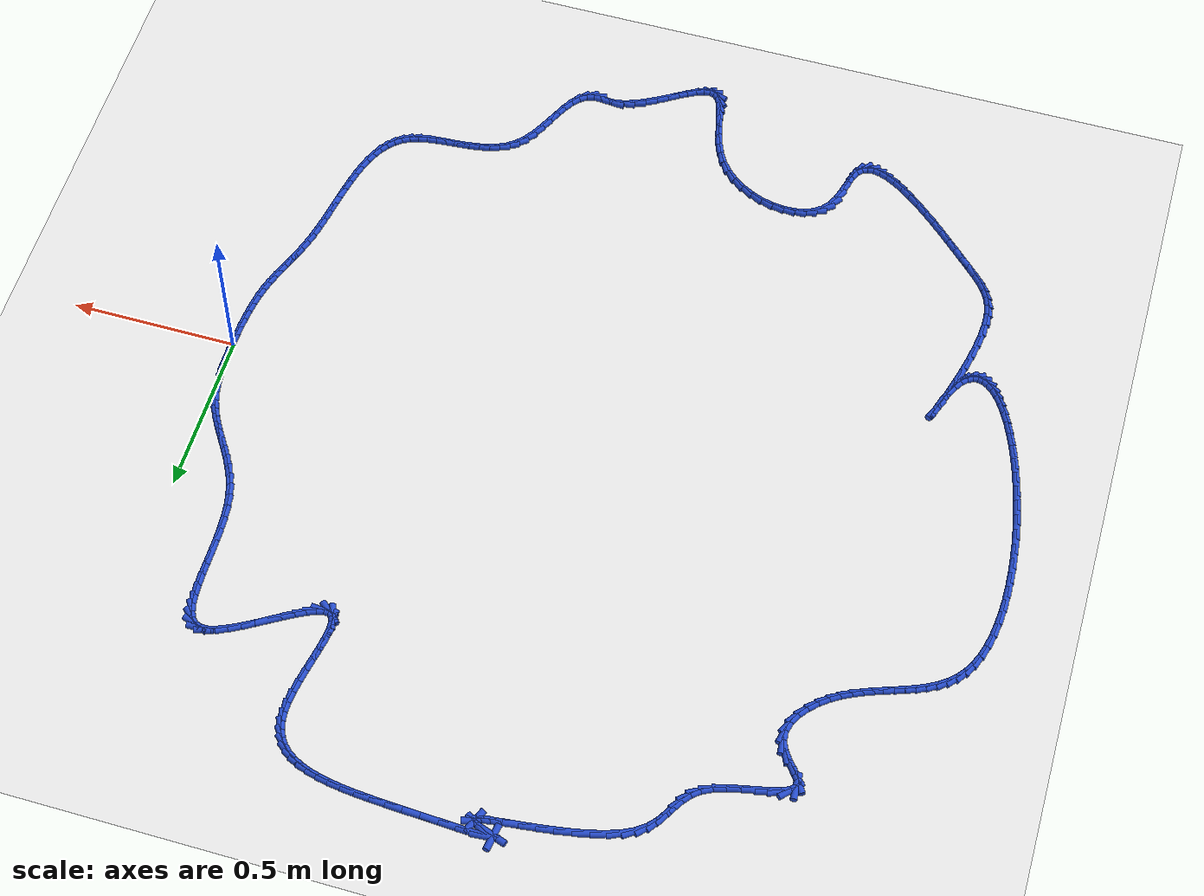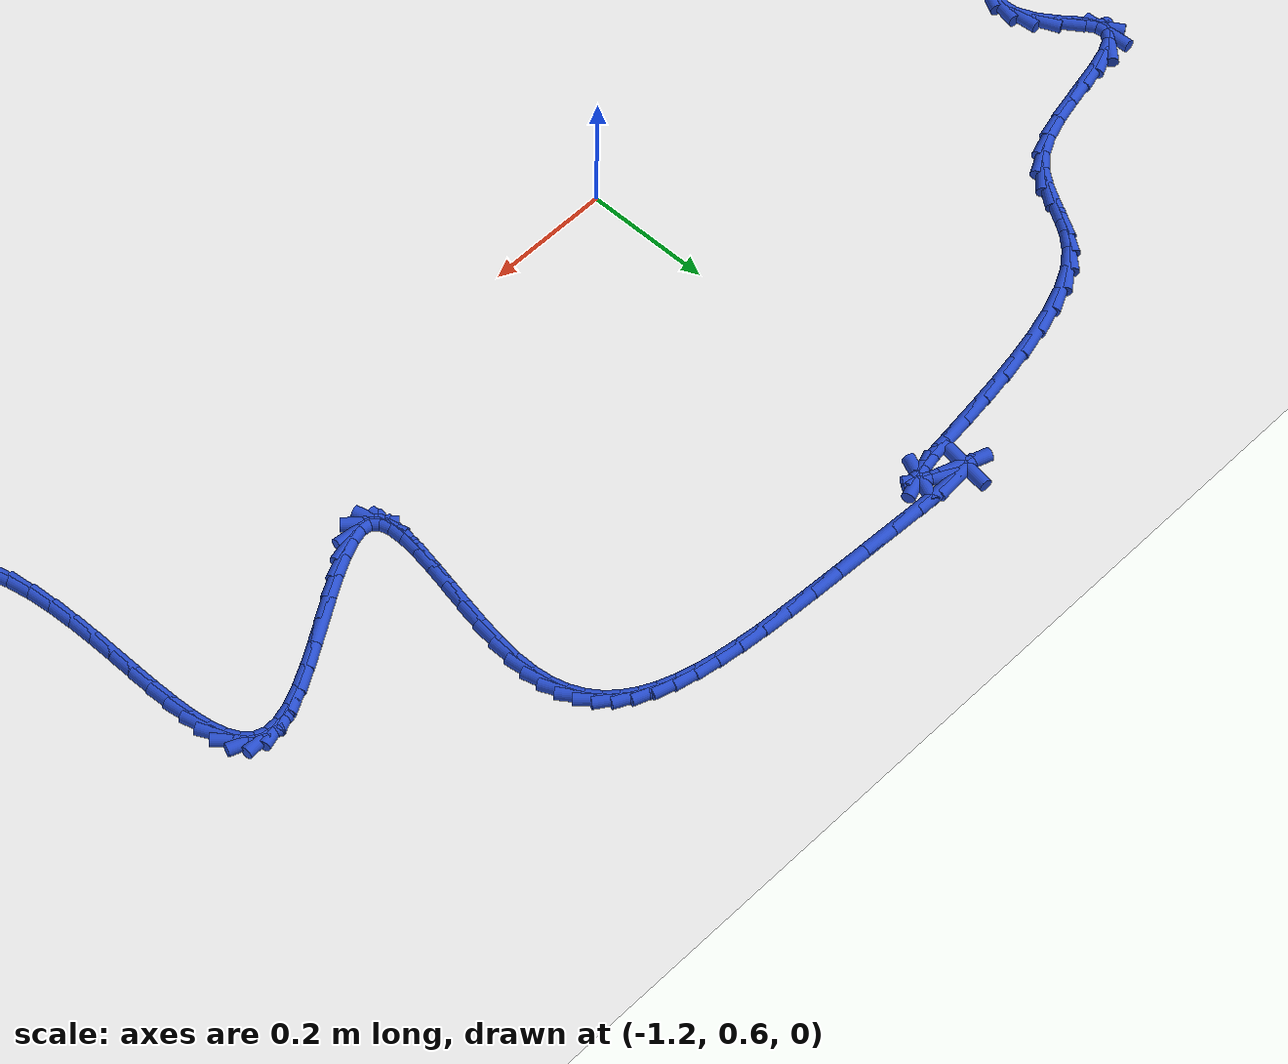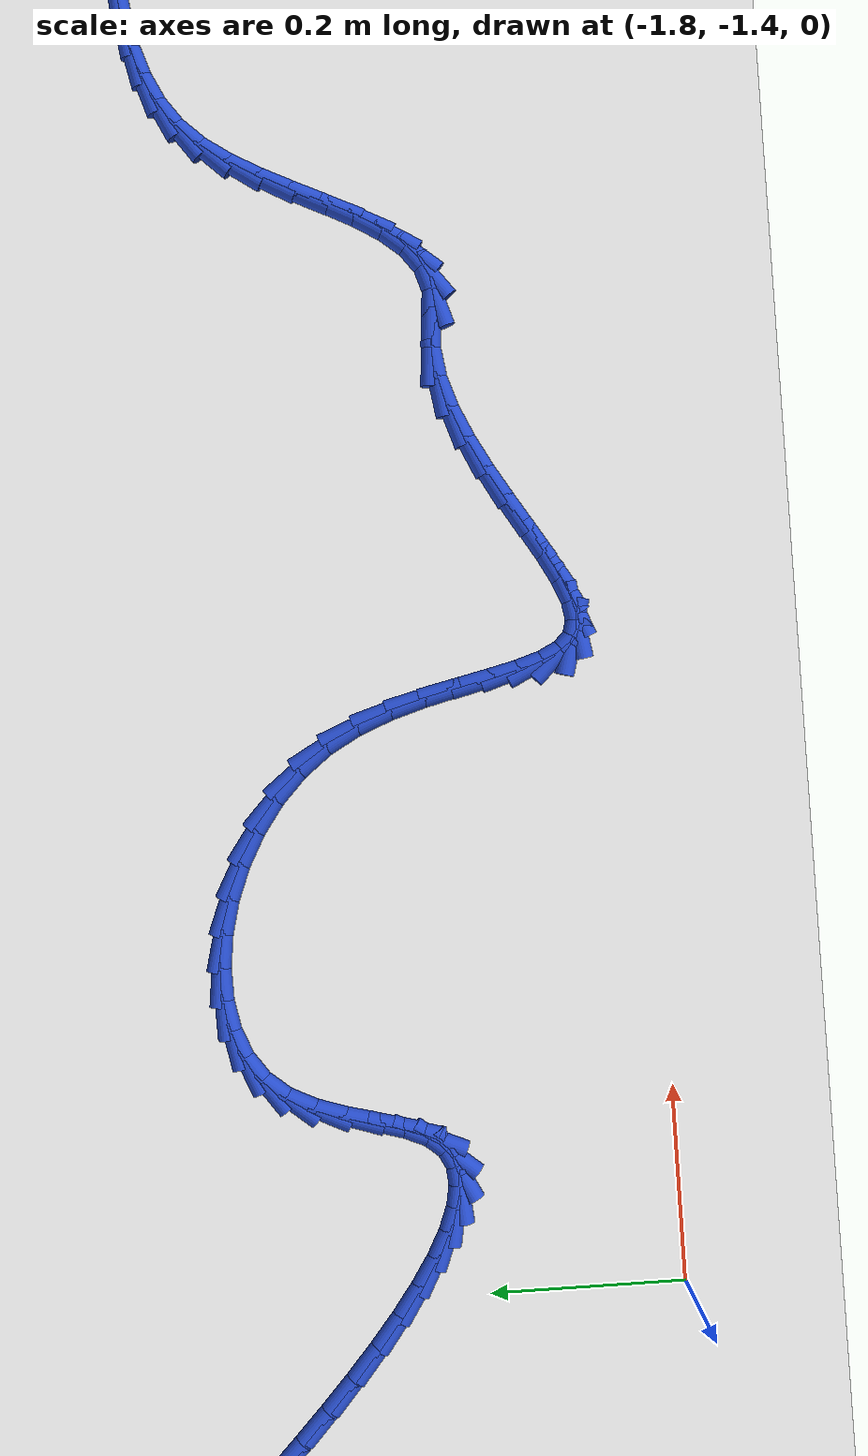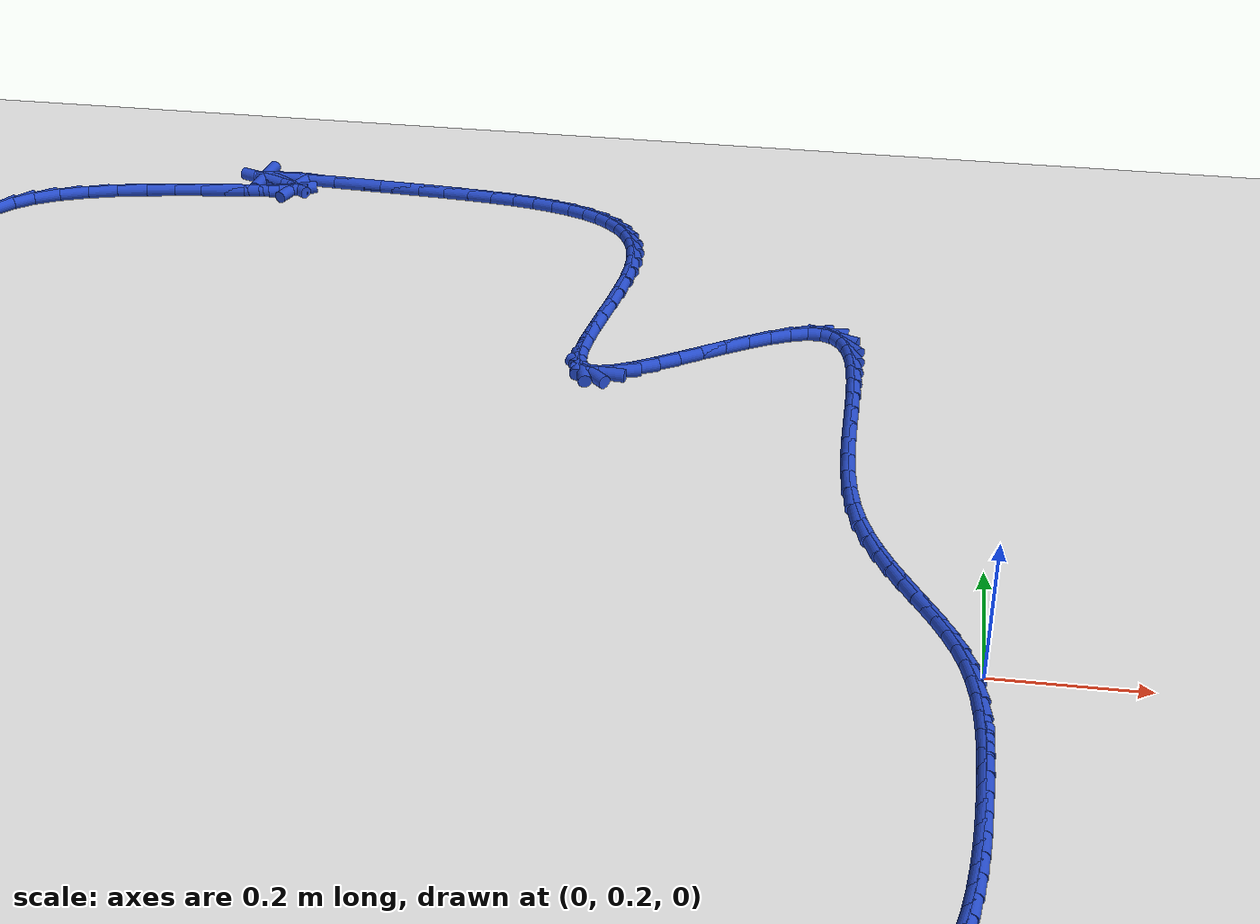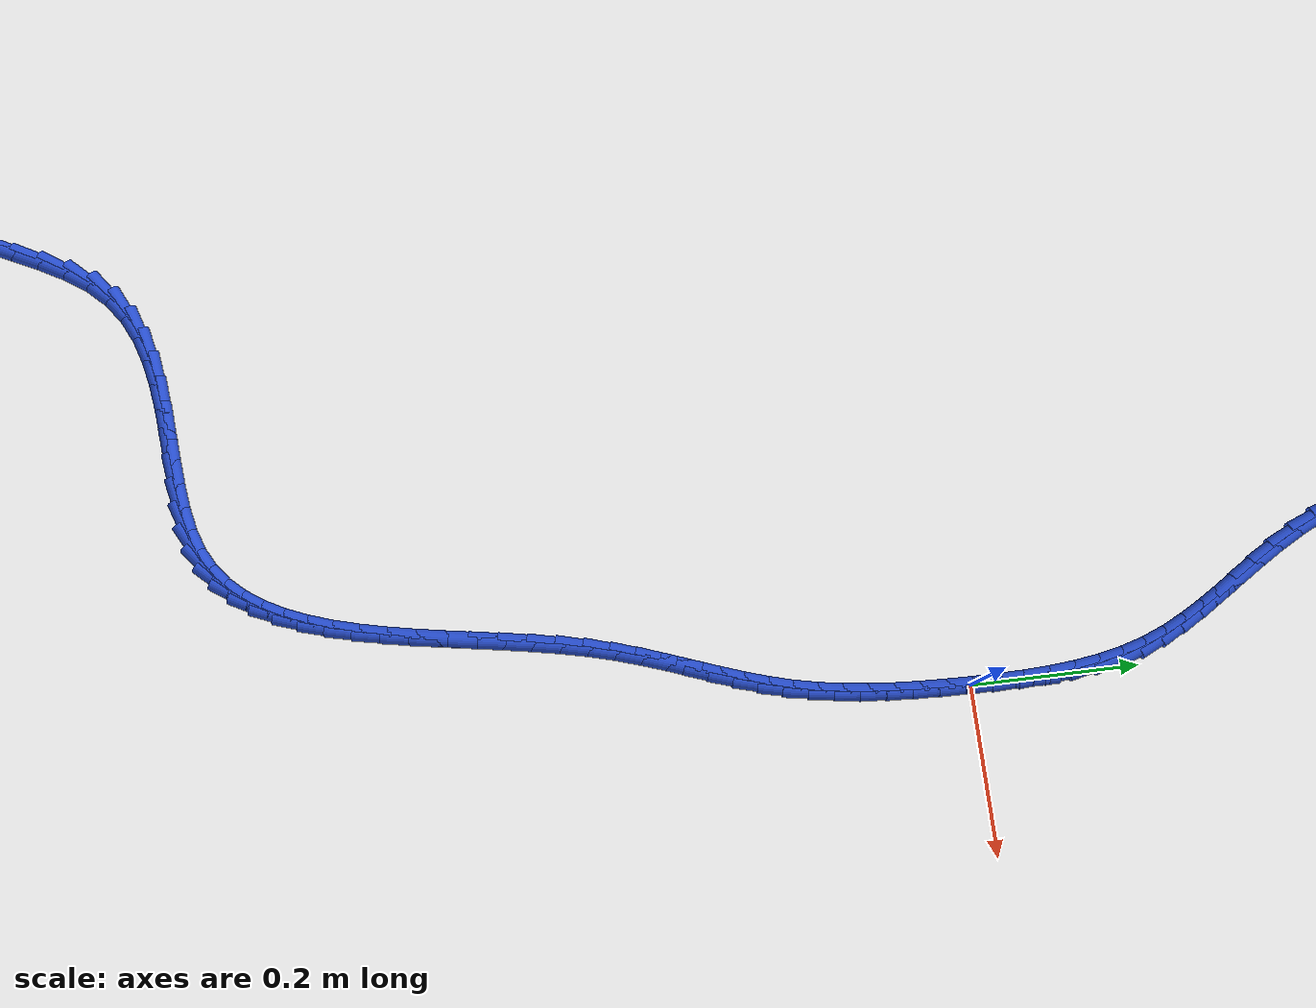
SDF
<sdf version="1.6">
 <world name="default">
  <light name="sun" type="directional">
   <pose>0 0 10 0 -0 0</pose>
   <diffuse>0.8 0.8 0.8 1</diffuse>
   <specular>0.2 0.2 0.2 1</specular>
   <attenuation>
    <range>1000</range>
    <constant>0.9</constant>
    <linear>0.01</linear>
    <quadratic>0.001</quadratic>
   </attenuation>
   <direction>-0.5 0.1 -0.9</direction>
  </light>
  <model name="ground_plane">
   <static>1</static>
   <link name="link">
    <collision name="collision">
     <geometry><plane><normal>0 0 1</normal><size>100 100</size></plane></geometry>
     <surface><friction><ode><mu>100</mu><mu2>50</mu2></ode></friction></surface>
    </collision>
    <visual name="visual">
     <cast_shadows>0</cast_shadows>
     <geometry><plane><normal>0 0 1</normal><size>100 100</size></plane></geometry>
     <material>
      <script><uri>file://media/materials/scripts/gazebo.material</uri><name>Gazebo/WhiteGlow</name></script>
     </material>
    </visual>
   </link>
  </model>
  <gravity>0 0 -9.8</gravity>
  <magnetic_field>6e-06 2.3e-05 -4.2e-05</magnetic_field>
  <atmosphere type="adiabatic"/>
  <physics name="default_physics" default="0" type="ode">
   <max_step_size>0.001</max_step_size>
   <real_time_factor>1</real_time_factor>
   <real_time_update_rate>1000</real_time_update_rate>
  </physics>
  <scene><ambient>0.4 0.4 0.4 1</ambient><background>0.7 0.7 0.7 1</background><shadows>1</shadows></scene>
  <spherical_coordinates>
   <surface_model>EARTH_WGS84</surface_model>
   <latitude_deg>0</latitude_deg>
   <longitude_deg>0</longitude_deg>
   <elevation>0</elevation>
   <heading_deg>0</heading_deg>
  </spherical_coordinates>
  <model name="line">
   <link name="link_0">
    <pose>6.776263578034403e-18 4.163336342344337e-17 0.01 0 1.57 1.5602584472414145</pose>
    <collision name="collision">
     <geometry><cylinder><radius>0.01</radius><length>0.08</length></cylinder></geometry>
    </collision>
    <visual name="visual">
     <material>
      <script><name>Gazebo/Blue</name><uri>file://media/materials/scripts/gazebo.material</uri></script>
     </material>
     <geometry><cylinder><radius>0.01</radius><length>0.08</length></cylinder></geometry>
    </visual>
   </link>
   <link name="link_1">
    <pose>0.000327550277992695 0.031081979231116937 0.01 0 1.57 -1.5604792286517062</pose>
    <collision name="collision">
     <geometry><cylinder><radius>0.01</radius><length>0.08</length></cylinder></geometry>
    </collision>
    <visual name="visual">
     <material>
      <script><name>Gazebo/Blue</name><uri>file://media/materials/scripts/gazebo.material</uri></script>
     </material>
     <geometry><cylinder><radius>0.01</radius><length>0.08</length></cylinder></geometry>
    </visual>
   </link>
   <link name="link_2">
    <pose>7.099979512376422e-06 0.062140996418618887 0.01 0 1.57 -1.5299403880837856</pose>
    <collision name="collision">
     <geometry><cylinder><radius>0.01</radius><length>0.08</length></cylinder></geometry>
    </collision>
    <visual name="visual">
     <material>
      <script><name>Gazebo/Blue</name><uri>file://media/materials/scripts/gazebo.material</uri></script>
     </material>
     <geometry><cylinder><radius>0.01</radius><length>0.08</length></cylinder></geometry>
    </visual>
   </link>
   <link name="link_3">
    <pose>-0.0012528439335075456 0.09296253274069599 0.01 0 1.57 -1.488958819356093</pose>
    <collision name="collision">
     <geometry><cylinder><radius>0.01</radius><length>0.08</length></cylinder></geometry>
    </collision>
    <visual name="visual">
     <material>
      <script><name>Gazebo/Blue</name><uri>file://media/materials/scripts/gazebo.material</uri></script>
     </material>
     <geometry><cylinder><radius>0.01</radius><length>0.08</length></cylinder></geometry>
    </visual>
   </link>
   <link name="link_4">
    <pose>-0.003743774499133664 0.12333206937553831 0.01 0 1.57 -1.4364917836941322</pose>
    <collision name="collision">
     <geometry><cylinder><radius>0.01</radius><length>0.08</length></cylinder></geometry>
    </collision>
    <visual name="visual">
     <material>
      <script><name>Gazebo/Blue</name><uri>file://media/materials/scripts/gazebo.material</uri></script>
     </material>
     <geometry><cylinder><radius>0.01</radius><length>0.08</length></cylinder></geometry>
    </visual>
   </link>
   <link name="link_5">
    <pose>-0.007757184755432579 0.15303508750133601 0.01 0 1.57 -1.3713003309995035</pose>
    <collision name="collision">
     <geometry><cylinder><radius>0.01</radius><length>0.08</length></cylinder></geometry>
    </collision>
    <visual name="visual">
     <material>
      <script><name>Gazebo/Blue</name><uri>file://media/materials/scripts/gazebo.material</uri></script>
     </material>
     <geometry><cylinder><radius>0.01</radius><length>0.08</length></cylinder></geometry>
    </visual>
   </link>
   <link name="link_6">
    <pose>-0.013584567740470883 0.18185706829627912 0.01 0 1.57 -1.292129476892571</pose>
    <collision name="collision">
     <geometry><cylinder><radius>0.01</radius><length>0.08</length></cylinder></geometry>
    </collision>
    <visual name="visual">
     <material>
      <script><name>Gazebo/Blue</name><uri>file://media/materials/scripts/gazebo.material</uri></script>
     </material>
     <geometry><cylinder><radius>0.01</radius><length>0.08</length></cylinder></geometry>
    </visual>
   </link>
   <link name="link_7">
    <pose>-0.021517416492315172 0.20958349293855782 0.01 0 1.57 -1.200821880152362</pose>
    <collision name="collision">
     <geometry><cylinder><radius>0.01</radius><length>0.08</length></cylinder></geometry>
    </collision>
    <visual name="visual">
     <material>
      <script><name>Gazebo/Blue</name><uri>file://media/materials/scripts/gazebo.material</uri></script>
     </material>
     <geometry><cylinder><radius>0.01</radius><length>0.08</length></cylinder></geometry>
    </visual>
   </link>
   <link name="link_8">
    <pose>-0.03178176420711263 0.23604933644428996 0.01 0 1.57 -1.1186853893705477</pose>
    <collision name="collision">
     <geometry><cylinder><radius>0.01</radius><length>0.08</length></cylinder></geometry>
    </collision>
    <visual name="visual">
     <material>
      <script><name>Gazebo/Blue</name><uri>file://media/materials/scripts/gazebo.material</uri></script>
     </material>
     <geometry><cylinder><radius>0.01</radius><length>0.08</length></cylinder></geometry>
    </visual>
   </link>
   <link name="link_9">
    <pose>-0.04412031726949272 0.26145501465825977 0.01 0 1.57 -1.0571818020051702</pose>
    <collision name="collision">
     <geometry><cylinder><radius>0.01</radius><length>0.08</length></cylinder></geometry>
    </collision>
    <visual name="visual">
     <material>
      <script><name>Gazebo/Blue</name><uri>file://media/materials/scripts/gazebo.material</uri></script>
     </material>
     <geometry><cylinder><radius>0.01</radius><length>0.08</length></cylinder></geometry>
    </visual>
   </link>
   <link name="link_10">
    <pose>-0.058059334336692574 0.2861645983994355 0.01 0 1.57 -1.017278763190798</pose>
    <collision name="collision">
     <geometry><cylinder><radius>0.01</radius><length>0.08</length></cylinder></geometry>
    </collision>
    <visual name="visual">
     <material>
      <script><name>Gazebo/Blue</name><uri>file://media/materials/scripts/gazebo.material</uri></script>
     </material>
     <geometry><cylinder><radius>0.01</radius><length>0.08</length></cylinder></geometry>
    </visual>
   </link>
   <link name="link_11">
    <pose>-0.07312405695429494 0.31054292751949136 0.01 0 1.57 -0.9988128582727365</pose>
    <collision name="collision">
     <geometry><cylinder><radius>0.01</radius><length>0.08</length></cylinder></geometry>
    </collision>
    <visual name="visual">
     <material>
      <script><name>Gazebo/Blue</name><uri>file://media/materials/scripts/gazebo.material</uri></script>
     </material>
     <geometry><cylinder><radius>0.01</radius><length>0.08</length></cylinder></geometry>
    </visual>
   </link>
   <link name="link_12">
    <pose>-0.08883972666788244 0.33495484187010166 0.01 0 1.57 -1.0011046139607211</pose>
    <collision name="collision">
     <geometry><cylinder><radius>0.01</radius><length>0.08</length></cylinder></geometry>
    </collision>
    <visual name="visual">
     <material>
      <script><name>Gazebo/Blue</name><uri>file://media/materials/scripts/gazebo.material</uri></script>
     </material>
     <geometry><cylinder><radius>0.01</radius><length>0.08</length></cylinder></geometry>
    </visual>
   </link>
   <link name="link_13">
    <pose>-0.10473158502303777 0.35976518130294044 0.01 0 1.57 -1.0232447133974558</pose>
    <collision name="collision">
     <geometry><cylinder><radius>0.01</radius><length>0.08</length></cylinder></geometry>
    </collision>
    <visual name="visual">
     <material>
      <script><name>Gazebo/Blue</name><uri>file://media/materials/scripts/gazebo.material</uri></script>
     </material>
     <geometry><cylinder><radius>0.01</radius><length>0.08</length></cylinder></geometry>
    </visual>
   </link>
   <link name="link_14">
    <pose>-0.12032487356534366 0.38533878566968244 0.01 0 1.57 -1.064107800309749</pose>
    <collision name="collision">
     <geometry><cylinder><radius>0.01</radius><length>0.08</length></cylinder></geometry>
    </collision>
    <visual name="visual">
     <material>
      <script><name>Gazebo/Blue</name><uri>file://media/materials/scripts/gazebo.material</uri></script>
     </material>
     <geometry><cylinder><radius>0.01</radius><length>0.08</length></cylinder></geometry>
    </visual>
   </link>
   <link name="link_15">
    <pose>-0.13514483384038273 0.41204049482200134 0.01 0 1.57 -1.1221688708951105</pose>
    <collision name="collision">
     <geometry><cylinder><radius>0.01</radius><length>0.08</length></cylinder></geometry>
    </collision>
    <visual name="visual">
     <material>
      <script><name>Gazebo/Blue</name><uri>file://media/materials/scripts/gazebo.material</uri></script>
     </material>
     <geometry><cylinder><radius>0.01</radius><length>0.08</length></cylinder></geometry>
    </visual>
   </link>
   <link name="link_16">
    <pose>-0.14871670739373774 0.4402351486115721 0.01 0 1.57 -1.1952320423755725</pose>
    <collision name="collision">
     <geometry><cylinder><radius>0.01</radius><length>0.08</length></cylinder></geometry>
    </collision>
    <visual name="visual">
     <material>
      <script><name>Gazebo/Blue</name><uri>file://media/materials/scripts/gazebo.material</uri></script>
     </material>
     <geometry><cylinder><radius>0.01</radius><length>0.08</length></cylinder></geometry>
    </visual>
   </link>
   <link name="link_17">
    <pose>-0.16056573577099126 0.4702875868900684 0.01 0 1.57 -1.2802236266488023</pose>
    <collision name="collision">
     <geometry><cylinder><radius>0.01</radius><length>0.08</length></cylinder></geometry>
    </collision>
    <visual name="visual">
     <material>
      <script><name>Gazebo/Blue</name><uri>file://media/materials/scripts/gazebo.material</uri></script>
     </material>
     <geometry><cylinder><radius>0.01</radius><length>0.08</length></cylinder></geometry>
    </visual>
   </link>
   <link name="link_18">
    <pose>-0.1702171605177262 0.5025626495091651 0.01 0 1.57 -1.371848461038212</pose>
    <collision name="collision">
     <geometry><cylinder><radius>0.01</radius><length>0.08</length></cylinder></geometry>
    </collision>
    <visual name="visual">
     <material>
      <script><name>Gazebo/Blue</name><uri>file://media/materials/scripts/gazebo.material</uri></script>
     </material>
     <geometry><cylinder><radius>0.01</radius><length>0.08</length></cylinder></geometry>
    </visual>
   </link>
   <link name="link_19">
    <pose>-0.17723706331857306 0.5373810224213147 0.01 0 1.57 -1.4495256472525202</pose>
    <collision name="collision">
     <geometry><cylinder><radius>0.01</radius><length>0.08</length></cylinder></geometry>
    </collision>
    <visual name="visual">
     <material>
      <script><name>Gazebo/Blue</name><uri>file://media/materials/scripts/gazebo.material</uri></script>
     </material>
     <geometry><cylinder><radius>0.01</radius><length>0.08</length></cylinder></geometry>
    </visual>
   </link>
   <link name="link_20">
    <pose>-0.18175510829779734 0.574454080180369 0.01 0 1.57 -1.5046508420633022</pose>
    <collision name="collision">
     <geometry><cylinder><radius>0.01</radius><length>0.08</length></cylinder></geometry>
    </collision>
    <visual name="visual">
     <material>
      <script><name>Gazebo/Blue</name><uri>file://media/materials/scripts/gazebo.material</uri></script>
     </material>
     <geometry><cylinder><radius>0.01</radius><length>0.08</length></cylinder></geometry>
    </visual>
   </link>
   <link name="link_21">
    <pose>-0.18431172447356337 0.6130491030703854 0.01 0 1.57 -1.541726305210649</pose>
    <collision name="collision">
     <geometry><cylinder><radius>0.01</radius><length>0.08</length></cylinder></geometry>
    </collision>
    <visual name="visual">
     <material>
      <script><name>Gazebo/Blue</name><uri>file://media/materials/scripts/gazebo.material</uri></script>
     </material>
     <geometry><cylinder><radius>0.01</radius><length>0.08</length></cylinder></geometry>
    </visual>
   </link>
   <link name="link_22">
    <pose>-0.18545665577946105 0.6524233006497441 0.01 0 1.57 -1.563615882027607</pose>
    <collision name="collision">
     <geometry><cylinder><radius>0.01</radius><length>0.08</length></cylinder></geometry>
    </collision>
    <visual name="visual">
     <material>
      <script><name>Gazebo/Blue</name><uri>file://media/materials/scripts/gazebo.material</uri></script>
     </material>
     <geometry><cylinder><radius>0.01</radius><length>0.08</length></cylinder></geometry>
    </visual>
   </link>
   <link name="link_23">
    <pose>-0.18573964614908062 0.691833882476826 0.01 0 1.57 1.5700417149979273</pose>
    <collision name="collision">
     <geometry><cylinder><radius>0.01</radius><length>0.08</length></cylinder></geometry>
    </collision>
    <visual name="visual">
     <material>
      <script><name>Gazebo/Blue</name><uri>file://media/materials/scripts/gazebo.material</uri></script>
     </material>
     <geometry><cylinder><radius>0.01</radius><length>0.08</length></cylinder></geometry>
    </visual>
   </link>
   <link name="link_24">
    <pose>-0.18571043951601204 0.730538058110012 0.01 0 1.57 -1.5652041044496232</pose>
    <collision name="collision">
     <geometry><cylinder><radius>0.01</radius><length>0.08</length></cylinder></geometry>
    </collision>
    <visual name="visual">
     <material>
      <script><name>Gazebo/Blue</name><uri>file://media/materials/scripts/gazebo.material</uri></script>
     </material>
     <geometry><cylinder><radius>0.01</radius><length>0.08</length></cylinder></geometry>
    </visual>
   </link>
   <link name="link_25">
    <pose>-0.18591877981384533 0.7677930371076824 0.01 0 1.57 -1.5424084556160356</pose>
    <collision name="collision">
     <geometry><cylinder><radius>0.01</radius><length>0.08</length></cylinder></geometry>
    </collision>
    <visual name="visual">
     <material>
      <script><name>Gazebo/Blue</name><uri>file://media/materials/scripts/gazebo.material</uri></script>
     </material>
     <geometry><cylinder><radius>0.01</radius><length>0.08</length></cylinder></geometry>
    </visual>
   </link>
   <link name="link_26">
    <pose>-0.18691441097617056 0.8028560290282181 0.01 0 1.57 -1.4983185978556681</pose>
    <collision name="collision">
     <geometry><cylinder><radius>0.01</radius><length>0.08</length></cylinder></geometry>
    </collision>
    <visual name="visual">
     <material>
      <script><name>Gazebo/Blue</name><uri>file://media/materials/scripts/gazebo.material</uri></script>
     </material>
     <geometry><cylinder><radius>0.01</radius><length>0.08</length></cylinder></geometry>
    </visual>
   </link>
   <link name="link_27">
    <pose>-0.18924707693657783 0.8349842434299994 0.01 0 1.57 -1.4235620301760807</pose>
    <collision name="collision">
     <geometry><cylinder><radius>0.01</radius><length>0.08</length></cylinder></geometry>
    </collision>
    <visual name="visual">
     <material>
      <script><name>Gazebo/Blue</name><uri>file://media/materials/scripts/gazebo.material</uri></script>
     </material>
     <geometry><cylinder><radius>0.01</radius><length>0.08</length></cylinder></geometry>
    </visual>
   </link>
   <link name="link_28">
    <pose>-0.19346652162865705 0.8634348898714073 0.01 0 1.57 -1.300588010641003</pose>
    <collision name="collision">
     <geometry><cylinder><radius>0.01</radius><length>0.08</length></cylinder></geometry>
    </collision>
    <visual name="visual">
     <material>
      <script><name>Gazebo/Blue</name><uri>file://media/materials/scripts/gazebo.material</uri></script>
     </material>
     <geometry><cylinder><radius>0.01</radius><length>0.08</length></cylinder></geometry>
    </visual>
   </link>
   <link name="link_29">
    <pose>-0.20012248898599844 0.8874651779108225 0.01 0 1.57 -1.0983401773954276</pose>
    <collision name="collision">
     <geometry><cylinder><radius>0.01</radius><length>0.08</length></cylinder></geometry>
    </collision>
    <visual name="visual">
     <material>
      <script><name>Gazebo/Blue</name><uri>file://media/materials/scripts/gazebo.material</uri></script>
     </material>
     <geometry><cylinder><radius>0.01</radius><length>0.08</length></cylinder></geometry>
    </visual>
   </link>
   <link name="link_30">
    <pose>-0.20976472294219184 0.906332317106625 0.01 0 1.57 -0.7770950186602225</pose>
    <collision name="collision">
     <geometry><cylinder><radius>0.01</radius><length>0.08</length></cylinder></geometry>
    </collision>
    <visual name="visual">
     <material>
      <script><name>Gazebo/Blue</name><uri>file://media/materials/scripts/gazebo.material</uri></script>
     </material>
     <geometry><cylinder><radius>0.01</radius><length>0.08</length></cylinder></geometry>
    </visual>
   </link>
   <link name="link_31">
    <pose>-0.2229429674308274 0.9192935170171959 0.01 0 1.57 -0.35054264638446914</pose>
    <collision name="collision">
     <geometry><cylinder><radius>0.01</radius><length>0.08</length></cylinder></geometry>
    </collision>
    <visual name="visual">
     <material>
      <script><name>Gazebo/Blue</name><uri>file://media/materials/scripts/gazebo.material</uri></script>
     </material>
     <geometry><cylinder><radius>0.01</radius><length>0.08</length></cylinder></geometry>
    </visual>
   </link>
   <link name="link_32">
    <pose>-0.24020696638549516 0.9256059872009157 0.01 0 1.57 0.042958525054722085</pose>
    <collision name="collision">
     <geometry><cylinder><radius>0.01</radius><length>0.08</length></cylinder></geometry>
    </collision>
    <visual name="visual">
     <material>
      <script><name>Gazebo/Blue</name><uri>file://media/materials/scripts/gazebo.material</uri></script>
     </material>
     <geometry><cylinder><radius>0.01</radius><length>0.08</length></cylinder></geometry>
    </visual>
   </link>
   <link name="link_33">
    <pose>-0.2620073682031355 0.9246688975763395 0.01 0 1.57 0.2822022993107532</pose>
    <collision name="collision">
     <geometry><cylinder><radius>0.01</radius><length>0.08</length></cylinder></geometry>
    </collision>
    <visual name="visual">
     <material>
      <script><name>Gazebo/Blue</name><uri>file://media/materials/scripts/gazebo.material</uri></script>
     </material>
     <geometry><cylinder><radius>0.01</radius><length>0.08</length></cylinder></geometry>
    </visual>
   </link>
   <link name="link_34">
    <pose>-0.28790150717281876 0.9171611446449733 0.01 0 1.57 0.4124817217138133</pose>
    <collision name="collision">
     <geometry><cylinder><radius>0.01</radius><length>0.08</length></cylinder></geometry>
    </collision>
    <visual name="visual">
     <material>
      <script><name>Gazebo/Blue</name><uri>file://media/materials/scripts/gazebo.material</uri></script>
     </material>
     <geometry><cylinder><radius>0.01</radius><length>0.08</length></cylinder></geometry>
    </visual>
   </link>
   <link name="link_35">
    <pose>-0.3169733582470942 0.9044397408374186 0.01 0 1.57 0.48654483667678783</pose>
    <collision name="collision">
     <geometry><cylinder><radius>0.01</radius><length>0.08</length></cylinder></geometry>
    </collision>
    <visual name="visual">
     <material>
      <script><name>Gazebo/Blue</name><uri>file://media/materials/scripts/gazebo.material</uri></script>
     </material>
     <geometry><cylinder><radius>0.01</radius><length>0.08</length></cylinder></geometry>
    </visual>
   </link>
   <link name="link_36">
    <pose>-0.34830256632770784 0.8878679016444005 0.01 0 1.57 0.5281605512984616</pose>
    <collision name="collision">
     <geometry><cylinder><radius>0.01</radius><length>0.08</length></cylinder></geometry>
    </collision>
    <visual name="visual">
     <material>
      <script><name>Gazebo/Blue</name><uri>file://media/materials/scripts/gazebo.material</uri></script>
     </material>
     <geometry><cylinder><radius>0.01</radius><length>0.08</length></cylinder></geometry>
    </visual>
   </link>
   <link name="link_37">
    <pose>-0.3809687763164051 0.868808842556643 0.01 0 1.57 0.5477955456250819</pose>
    <collision name="collision">
     <geometry><cylinder><radius>0.01</radius><length>0.08</length></cylinder></geometry>
    </collision>
    <visual name="visual">
     <material>
      <script><name>Gazebo/Blue</name><uri>file://media/materials/scripts/gazebo.material</uri></script>
     </material>
     <geometry><cylinder><radius>0.01</radius><length>0.08</length></cylinder></geometry>
    </visual>
   </link>
   <link name="link_38">
    <pose>-0.41405163311493126 0.8486257790648706 0.01 0 1.57 0.5493172159844522</pose>
    <collision name="collision">
     <geometry><cylinder><radius>0.01</radius><length>0.08</length></cylinder></geometry>
    </collision>
    <visual name="visual">
     <material>
      <script><name>Gazebo/Blue</name><uri>file://media/materials/scripts/gazebo.material</uri></script>
     </material>
     <geometry><cylinder><radius>0.01</radius><length>0.08</length></cylinder></geometry>
    </visual>
   </link>
   <link name="link_39">
    <pose>-0.44663078162503245 0.8286819266598072 0.01 0 1.57 0.5320794246308768</pose>
    <collision name="collision">
     <geometry><cylinder><radius>0.01</radius><length>0.08</length></cylinder></geometry>
    </collision>
    <visual name="visual">
     <material>
      <script><name>Gazebo/Blue</name><uri>file://media/materials/scripts/gazebo.material</uri></script>
     </material>
     <geometry><cylinder><radius>0.01</radius><length>0.08</length></cylinder></geometry>
    </visual>
   </link>
   <link name="link_40">
    <pose>-0.47778586674845436 0.8103405008321778 0.01 0 1.57 0.4902300792805051</pose>
    <collision name="collision">
     <geometry><cylinder><radius>0.01</radius><length>0.08</length></cylinder></geometry>
    </collision>
    <visual name="visual">
     <material>
      <script><name>Gazebo/Blue</name><uri>file://media/materials/scripts/gazebo.material</uri></script>
     </material>
     <geometry><cylinder><radius>0.01</radius><length>0.08</length></cylinder></geometry>
    </visual>
   </link>
   <link name="link_41">
    <pose>-0.5065965333869424 0.7949647170727063 0.01 0 1.57 0.40815086902002784</pose>
    <collision name="collision">
     <geometry><cylinder><radius>0.01</radius><length>0.08</length></cylinder></geometry>
    </collision>
    <visual name="visual">
     <material>
      <script><name>Gazebo/Blue</name><uri>file://media/materials/scripts/gazebo.material</uri></script>
     </material>
     <geometry><cylinder><radius>0.01</radius><length>0.08</length></cylinder></geometry>
    </visual>
   </link>
   <link name="link_42">
    <pose>-0.5321424264422424 0.7839177908721174 0.01 0 1.57 0.2456245835175273</pose>
    <collision name="collision">
     <geometry><cylinder><radius>0.01</radius><length>0.08</length></cylinder></geometry>
    </collision>
    <visual name="visual">
     <material>
      <script><name>Gazebo/Blue</name><uri>file://media/materials/scripts/gazebo.material</uri></script>
     </material>
     <geometry><cylinder><radius>0.01</radius><length>0.08</length></cylinder></geometry>
    </visual>
   </link>
   <link name="link_43">
    <pose>-0.5535031908160996 0.778562937721135 0.01 0 1.57 -0.10422909891074461</pose>
    <collision name="collision">
     <geometry><cylinder><radius>0.01</radius><length>0.08</length></cylinder></geometry>
    </collision>
    <visual name="visual">
     <material>
      <script><name>Gazebo/Blue</name><uri>file://media/materials/scripts/gazebo.material</uri></script>
     </material>
     <geometry><cylinder><radius>0.01</radius><length>0.08</length></cylinder></geometry>
    </visual>
   </link>
   <link name="link_44">
    <pose>-0.5697584714102601 0.7802633731104844 0.01 0 1.57 -0.7570392654841966</pose>
    <collision name="collision">
     <geometry><cylinder><radius>0.01</radius><length>0.08</length></cylinder></geometry>
    </collision>
    <visual name="visual">
     <material>
      <script><name>Gazebo/Blue</name><uri>file://media/materials/scripts/gazebo.material</uri></script>
     </material>
     <geometry><cylinder><radius>0.01</radius><length>0.08</length></cylinder></geometry>
    </visual>
   </link>
   <link name="link_45">
    <pose>-0.5801843101157783 0.7901140383133227 0.01 0 1.57 -1.286753402161795</pose>
    <collision name="collision">
     <geometry><cylinder><radius>0.01</radius><length>0.08</length></cylinder></geometry>
    </collision>
    <visual name="visual">
     <material>
      <script><name>Gazebo/Blue</name><uri>file://media/materials/scripts/gazebo.material</uri></script>
     </material>
     <geometry><cylinder><radius>0.01</radius><length>0.08</length></cylinder></geometry>
    </visual>
   </link>
   <link name="link_46">
    <pose>-0.5852737642220837 0.8075474567881864 0.01 0 1.57 -1.540918213273077</pose>
    <collision name="collision">
     <geometry><cylinder><radius>0.01</radius><length>0.08</length></cylinder></geometry>
    </collision>
    <visual name="visual">
     <material>
      <script><name>Gazebo/Blue</name><uri>file://media/materials/scripts/gazebo.material</uri></script>
     </material>
     <geometry><cylinder><radius>0.01</radius><length>0.08</length></cylinder></geometry>
    </visual>
   </link>
   <link name="link_47">
    <pose>-0.5859854558578569 0.8313602000708465 0.01 0 1.57 1.477697612081155</pose>
    <collision name="collision">
     <geometry><cylinder><radius>0.01</radius><length>0.08</length></cylinder></geometry>
    </collision>
    <visual name="visual">
     <material>
      <script><name>Gazebo/Blue</name><uri>file://media/materials/scripts/gazebo.material</uri></script>
     </material>
     <geometry><cylinder><radius>0.01</radius><length>0.08</length></cylinder></geometry>
    </visual>
   </link>
   <link name="link_48">
    <pose>-0.5832789462277708 0.8603475569387273 0.01 0 1.57 1.415338212089694</pose>
    <collision name="collision">
     <geometry><cylinder><radius>0.01</radius><length>0.08</length></cylinder></geometry>
    </collision>
    <visual name="visual">
     <material>
      <script><name>Gazebo/Blue</name><uri>file://media/materials/scripts/gazebo.material</uri></script>
     </material>
     <geometry><cylinder><radius>0.01</radius><length>0.08</length></cylinder></geometry>
    </visual>
   </link>
   <link name="link_49">
    <pose>-0.5781137965364982 0.8933048161692537 0.01 0 1.57 1.386360712986718</pose>
    <collision name="collision">
     <geometry><cylinder><radius>0.01</radius><length>0.08</length></cylinder></geometry>
    </collision>
    <visual name="visual">
     <material>
      <script><name>Gazebo/Blue</name><uri>file://media/materials/scripts/gazebo.material</uri></script>
     </material>
     <geometry><cylinder><radius>0.01</radius><length>0.08</length></cylinder></geometry>
    </visual>
   </link>
   <link name="link_50">
    <pose>-0.5714495679887123 0.9290272665398503 0.01 0 1.57 1.3799300086938708</pose>
    <collision name="collision">
     <geometry><cylinder><radius>0.01</radius><length>0.08</length></cylinder></geometry>
    </collision>
    <visual name="visual">
     <material>
      <script><name>Gazebo/Blue</name><uri>file://media/materials/scripts/gazebo.material</uri></script>
     </material>
     <geometry><cylinder><radius>0.01</radius><length>0.08</length></cylinder></geometry>
    </visual>
   </link>
   <link name="link_51">
    <pose>-0.5642458217890863 0.9663101968279415 0.01 0 1.57 1.3924785588561355</pose>
    <collision name="collision">
     <geometry><cylinder><radius>0.01</radius><length>0.08</length></cylinder></geometry>
    </collision>
    <visual name="visual">
     <material>
      <script><name>Gazebo/Blue</name><uri>file://media/materials/scripts/gazebo.material</uri></script>
     </material>
     <geometry><cylinder><radius>0.01</radius><length>0.08</length></cylinder></geometry>
    </visual>
   </link>
   <link name="link_52">
    <pose>-0.5574621191422929 1.0039488958109524 0.01 0 1.57 1.4249479775227054</pose>
    <collision name="collision">
     <geometry><cylinder><radius>0.01</radius><length>0.08</length></cylinder></geometry>
    </collision>
    <visual name="visual">
     <material>
      <script><name>Gazebo/Blue</name><uri>file://media/materials/scripts/gazebo.material</uri></script>
     </material>
     <geometry><cylinder><radius>0.01</radius><length>0.08</length></cylinder></geometry>
    </visual>
   </link>
   <link name="link_53">
    <pose>-0.5520580212530052 1.0407386522663071 0.01 0 1.57 1.4827894763573972</pose>
    <collision name="collision">
     <geometry><cylinder><radius>0.01</radius><length>0.08</length></cylinder></geometry>
    </collision>
    <visual name="visual">
     <material>
      <script><name>Gazebo/Blue</name><uri>file://media/materials/scripts/gazebo.material</uri></script>
     </material>
     <geometry><cylinder><radius>0.01</radius><length>0.08</length></cylinder></geometry>
    </visual>
   </link>
   <link name="link_54">
    <pose>-0.5489930893258962 1.0754747549714303 0.01 0 1.57 -1.565199393456655</pose>
    <collision name="collision">
     <geometry><cylinder><radius>0.01</radius><length>0.08</length></cylinder></geometry>
    </collision>
    <visual name="visual">
     <material>
      <script><name>Gazebo/Blue</name><uri>file://media/materials/scripts/gazebo.material</uri></script>
     </material>
     <geometry><cylinder><radius>0.01</radius><length>0.08</length></cylinder></geometry>
    </visual>
   </link>
   <link name="link_55">
    <pose>-0.5491697137560657 1.107031783651125 0.01 0 1.57 -1.4392343606792386</pose>
    <collision name="collision">
     <geometry><cylinder><radius>0.01</radius><length>0.08</length></cylinder></geometry>
    </collision>
    <visual name="visual">
     <material>
      <script><name>Gazebo/Blue</name><uri>file://media/materials/scripts/gazebo.material</uri></script>
     </material>
     <geometry><cylinder><radius>0.01</radius><length>0.08</length></cylinder></geometry>
    </visual>
   </link>
   <link name="link_56">
    <pose>-0.5528867118132508 1.1351214215324674 0.01 0 1.57 -1.2888583824309638</pose>
    <collision name="collision">
     <geometry><cylinder><radius>0.01</radius><length>0.08</length></cylinder></geometry>
    </collision>
    <visual name="visual">
     <material>
      <script><name>Gazebo/Blue</name><uri>file://media/materials/scripts/gazebo.material</uri></script>
     </material>
     <geometry><cylinder><radius>0.01</radius><length>0.08</length></cylinder></geometry>
    </visual>
   </link>
   <link name="link_57">
    <pose>-0.5600806496020614 1.1599577627456865 0.01 0 1.57 -1.1181966708477344</pose>
    <collision name="collision">
     <geometry><cylinder><radius>0.01</radius><length>0.08</length></cylinder></geometry>
    </collision>
    <visual name="visual">
     <material>
      <script><name>Gazebo/Blue</name><uri>file://media/materials/scripts/gazebo.material</uri></script>
     </material>
     <geometry><cylinder><radius>0.01</radius><length>0.08</length></cylinder></geometry>
    </visual>
   </link>
   <link name="link_58">
    <pose>-0.5706831661540217 1.1817617348434455 0.01 0 1.57 -0.9375382500278301</pose>
    <collision name="collision">
     <geometry><cylinder><radius>0.01</radius><length>0.08</length></cylinder></geometry>
    </collision>
    <visual name="visual">
     <material>
      <script><name>Gazebo/Blue</name><uri>file://media/materials/scripts/gazebo.material</uri></script>
     </material>
     <geometry><cylinder><radius>0.01</radius><length>0.08</length></cylinder></geometry>
    </visual>
   </link>
   <link name="link_59">
    <pose>-0.584625900500656 1.2007542653784071 0.01 0 1.57 -0.7612310477101222</pose>
    <collision name="collision">
     <geometry><cylinder><radius>0.01</radius><length>0.08</length></cylinder></geometry>
    </collision>
    <visual name="visual">
     <material>
      <script><name>Gazebo/Blue</name><uri>file://media/materials/scripts/gazebo.material</uri></script>
     </material>
     <geometry><cylinder><radius>0.01</radius><length>0.08</length></cylinder></geometry>
    </visual>
   </link>
   <link name="link_60">
    <pose>-0.6018404916734886 1.2171562819032347 0.01 0 1.57 -0.6021208833909827</pose>
    <collision name="collision">
     <geometry><cylinder><radius>0.01</radius><length>0.08</length></cylinder></geometry>
    </collision>
    <visual name="visual">
     <material>
      <script><name>Gazebo/Blue</name><uri>file://media/materials/scripts/gazebo.material</uri></script>
     </material>
     <geometry><cylinder><radius>0.01</radius><length>0.08</length></cylinder></geometry>
    </visual>
   </link>
   <link name="link_61">
    <pose>-0.6222585787040439 1.2311887119705918 0.01 0 1.57 -0.46728074480648657</pose>
    <collision name="collision">
     <geometry><cylinder><radius>0.01</radius><length>0.08</length></cylinder></geometry>
    </collision>
    <visual name="visual">
     <material>
      <script><name>Gazebo/Blue</name><uri>file://media/materials/scripts/gazebo.material</uri></script>
     </material>
     <geometry><cylinder><radius>0.01</radius><length>0.08</length></cylinder></geometry>
    </visual>
   </link>
   <link name="link_62">
    <pose>-0.6458118006238462 1.2430724831331412 0.01 0 1.57 -0.3578989878049125</pose>
    <collision name="collision">
     <geometry><cylinder><radius>0.01</radius><length>0.08</length></cylinder></geometry>
    </collision>
    <visual name="visual">
     <material>
      <script><name>Gazebo/Blue</name><uri>file://media/materials/scripts/gazebo.material</uri></script>
     </material>
     <geometry><cylinder><radius>0.01</radius><length>0.08</length></cylinder></geometry>
    </visual>
   </link>
   <link name="link_63">
    <pose>-0.67243179646442 1.253028522943546 0.01 0 1.57 -0.27163316577395574</pose>
    <collision name="collision">
     <geometry><cylinder><radius>0.01</radius><length>0.08</length></cylinder></geometry>
    </collision>
    <visual name="visual">
     <material>
      <script><name>Gazebo/Blue</name><uri>file://media/materials/scripts/gazebo.material</uri></script>
     </material>
     <geometry><cylinder><radius>0.01</radius><length>0.08</length></cylinder></geometry>
    </visual>
   </link>
   <link name="link_64">
    <pose>-0.7020502052572891 1.2612777589544693 0.01 0 1.57 -0.2048779905038701</pose>
    <collision name="collision">
     <geometry><cylinder><radius>0.01</radius><length>0.08</length></cylinder></geometry>
    </collision>
    <visual name="visual">
     <material>
      <script><name>Gazebo/Blue</name><uri>file://media/materials/scripts/gazebo.material</uri></script>
     </material>
     <geometry><cylinder><radius>0.01</radius><length>0.08</length></cylinder></geometry>
    </visual>
   </link>
   <link name="link_65">
    <pose>-0.7345986660339785 1.268041118718575 0.01 0 1.57 -0.15404758774661984</pose>
    <collision name="collision">
     <geometry><cylinder><radius>0.01</radius><length>0.08</length></cylinder></geometry>
    </collision>
    <visual name="visual">
     <material>
      <script><name>Gazebo/Blue</name><uri>file://media/materials/scripts/gazebo.material</uri></script>
     </material>
     <geometry><cylinder><radius>0.01</radius><length>0.08</length></cylinder></geometry>
    </visual>
   </link>
   <link name="link_66">
    <pose>-0.7700088178260117 1.273539529788525 0.01 0 1.57 -0.1160723414007952</pose>
    <collision name="collision">
     <geometry><cylinder><radius>0.01</radius><length>0.08</length></cylinder></geometry>
    </collision>
    <visual name="visual">
     <material>
      <script><name>Gazebo/Blue</name><uri>file://media/materials/scripts/gazebo.material</uri></script>
     </material>
     <geometry><cylinder><radius>0.01</radius><length>0.08</length></cylinder></geometry>
    </visual>
   </link>
   <link name="link_67">
    <pose>-0.8082122996649135 1.2779939197169834 0.01 0 1.57 -0.08849132469356645</pose>
    <collision name="collision">
     <geometry><cylinder><radius>0.01</radius><length>0.08</length></cylinder></geometry>
    </collision>
    <visual name="visual">
     <material>
      <script><name>Gazebo/Blue</name><uri>file://media/materials/scripts/gazebo.material</uri></script>
     </material>
     <geometry><cylinder><radius>0.01</radius><length>0.08</length></cylinder></geometry>
    </visual>
   </link>
   <link name="link_68">
    <pose>-0.8491407505822082 1.2816252160566133 0.01 0 1.57 -0.06938770773945288</pose>
    <collision name="collision">
     <geometry><cylinder><radius>0.01</radius><length>0.08</length></cylinder></geometry>
    </collision>
    <visual name="visual">
     <material>
      <script><name>Gazebo/Blue</name><uri>file://media/materials/scripts/gazebo.material</uri></script>
     </material>
     <geometry><cylinder><radius>0.01</radius><length>0.08</length></cylinder></geometry>
    </visual>
   </link>
   <link name="link_69">
    <pose>-0.8927258096094203 1.2846543463600775 0.01 0 1.57 -0.05728406918525061</pose>
    <collision name="collision">
     <geometry><cylinder><radius>0.01</radius><length>0.08</length></cylinder></geometry>
    </collision>
    <visual name="visual">
     <material>
      <script><name>Gazebo/Blue</name><uri>file://media/materials/scripts/gazebo.material</uri></script>
     </material>
     <geometry><cylinder><radius>0.01</radius><length>0.08</length></cylinder></geometry>
    </visual>
   </link>
   <link name="link_70">
    <pose>-0.9388991157780733 1.2873022381800392 0.01 0 1.57 -0.05104245725569193</pose>
    <collision name="collision">
     <geometry><cylinder><radius>0.01</radius><length>0.08</length></cylinder></geometry>
    </collision>
    <visual name="visual">
     <material>
      <script><name>Gazebo/Blue</name><uri>file://media/materials/scripts/gazebo.material</uri></script>
     </material>
     <geometry><cylinder><radius>0.01</radius><length>0.08</length></cylinder></geometry>
    </visual>
   </link>
   <link name="link_71">
    <pose>-0.9875923081196922 1.2897898190691617 0.01 0 1.57 -0.04978206733143617</pose>
    <collision name="collision">
     <geometry><cylinder><radius>0.01</radius><length>0.08</length></cylinder></geometry>
    </collision>
    <visual name="visual">
     <material>
      <script><name>Gazebo/Blue</name><uri>file://media/materials/scripts/gazebo.material</uri></script>
     </material>
     <geometry><cylinder><radius>0.01</radius><length>0.08</length></cylinder></geometry>
    </visual>
   </link>
   <link name="link_72">
    <pose>-1.038737007489423 1.2923380133090823 0.01 0 1.57 -0.05020717658423297</pose>
    <collision name="collision">
     <geometry><cylinder><radius>0.01</radius><length>0.08</length></cylinder></geometry>
    </collision>
    <visual name="visual">
     <material>
      <script><name>Gazebo/Blue</name><uri>file://media/materials/scripts/gazebo.material</uri></script>
     </material>
     <geometry><cylinder><radius>0.01</radius><length>0.08</length></cylinder></geometry>
    </visual>
   </link>
   <link name="link_73">
    <pose>-1.0911855852749217 1.2949735231842554 0.01 0 1.57 -0.0417640791201011</pose>
    <collision name="collision">
     <geometry><cylinder><radius>0.01</radius><length>0.08</length></cylinder></geometry>
    </collision>
    <visual name="visual">
     <material>
      <script><name>Gazebo/Blue</name><uri>file://media/materials/scripts/gazebo.material</uri></script>
     </material>
     <geometry><cylinder><radius>0.01</radius><length>0.08</length></cylinder></geometry>
    </visual>
   </link>
   <link name="link_74">
    <pose>-1.1398007630145084 1.2970050726199627 0.01 0 1.57 -0.014730425114433753</pose>
    <collision name="collision">
     <geometry><cylinder><radius>0.01</radius><length>0.08</length></cylinder></geometry>
    </collision>
    <visual name="visual">
     <material>
      <script><name>Gazebo/Blue</name><uri>file://media/materials/scripts/gazebo.material</uri></script>
     </material>
     <geometry><cylinder><radius>0.01</radius><length>0.08</length></cylinder></geometry>
    </visual>
   </link>
   <link name="link_75">
    <pose>-1.1785235682344721 1.297575517262464 0.01 0 1.57 0.07660397466082268</pose>
    <collision name="collision">
     <geometry><cylinder><radius>0.01</radius><length>0.08</length></cylinder></geometry>
    </collision>
    <visual name="visual">
     <material>
      <script><name>Gazebo/Blue</name><uri>file://media/materials/scripts/gazebo.material</uri></script>
     </material>
     <geometry><cylinder><radius>0.01</radius><length>0.08</length></cylinder></geometry>
    </visual>
   </link>
   <link name="link_76">
    <pose>-1.2012950284611015 1.295827712758019 0.01 0 1.57 1.417407422681616</pose>
    <collision name="collision">
     <geometry><cylinder><radius>0.01</radius><length>0.08</length></cylinder></geometry>
    </collision>
    <visual name="visual">
     <material>
      <script><name>Gazebo/Blue</name><uri>file://media/materials/scripts/gazebo.material</uri></script>
     </material>
     <geometry><cylinder><radius>0.01</radius><length>0.08</length></cylinder></geometry>
    </visual>
   </link>
   <link name="link_77">
    <pose>-1.202056171220686 1.2909045147528868 0.01 0 1.57 -0.3369684409657891</pose>
    <collision name="collision">
     <geometry><cylinder><radius>0.01</radius><length>0.08</length></cylinder></geometry>
    </collision>
    <visual name="visual">
     <material>
      <script><name>Gazebo/Blue</name><uri>file://media/materials/scripts/gazebo.material</uri></script>
     </material>
     <geometry><cylinder><radius>0.01</radius><length>0.08</length></cylinder></geometry>
    </visual>
   </link>
   <link name="link_78">
    <pose>-1.1776069640310076 1.2823392331884216 0.01 0 1.57 -0.33609467461101733</pose>
    <collision name="collision">
     <geometry><cylinder><radius>0.01</radius><length>0.08</length></cylinder></geometry>
    </collision>
    <visual name="visual">
     <material>
      <script><name>Gazebo/Blue</name><uri>file://media/materials/scripts/gazebo.material</uri></script>
     </material>
     <geometry><cylinder><radius>0.01</radius><length>0.08</length></cylinder></geometry>
    </visual>
   </link>
   <link name="link_79">
    <pose>-1.1519449479625414 1.2733742355996696 0.01 0 1.57 -0.5903008592595691</pose>
    <collision name="collision">
     <geometry><cylinder><radius>0.01</radius><length>0.08</length></cylinder></geometry>
    </collision>
    <visual name="visual">
     <material>
      <script><name>Gazebo/Blue</name><uri>file://media/materials/scripts/gazebo.material</uri></script>
     </material>
     <geometry><cylinder><radius>0.01</radius><length>0.08</length></cylinder></geometry>
    </visual>
   </link>
   <link name="link_80">
    <pose>-1.1410711649326697 1.2660888937297645 0.01 0 1.57 1.1670317731154</pose>
    <collision name="collision">
     <geometry><cylinder><radius>0.01</radius><length>0.08</length></cylinder></geometry>
    </collision>
    <visual name="visual">
     <material>
      <script><name>Gazebo/Blue</name><uri>file://media/materials/scripts/gazebo.material</uri></script>
     </material>
     <geometry><cylinder><radius>0.01</radius><length>0.08</length></cylinder></geometry>
    </visual>
   </link>
   <link name="link_81">
    <pose>-1.1436128139027044 1.2601398672434556 0.01 0 1.57 0.33862461294450813</pose>
    <collision name="collision">
     <geometry><cylinder><radius>0.01</radius><length>0.08</length></cylinder></geometry>
    </collision>
    <visual name="visual">
     <material>
      <script><name>Gazebo/Blue</name><uri>file://media/materials/scripts/gazebo.material</uri></script>
     </material>
     <geometry><cylinder><radius>0.01</radius><length>0.08</length></cylinder></geometry>
    </visual>
   </link>
   <link name="link_82">
    <pose>-1.1578301539507612 1.2551326602521653 0.01 0 1.57 0.18259246054484896</pose>
    <collision name="collision">
     <geometry><cylinder><radius>0.01</radius><length>0.08</length></cylinder></geometry>
    </collision>
    <visual name="visual">
     <material>
      <script><name>Gazebo/Blue</name><uri>file://media/materials/scripts/gazebo.material</uri></script>
     </material>
     <geometry><cylinder><radius>0.01</radius><length>0.08</length></cylinder></geometry>
    </visual>
   </link>
   <link name="link_83">
    <pose>-1.1819834441549562 1.2506727768673178 0.01 0 1.57 0.13236288670499563</pose>
    <collision name="collision">
     <geometry><cylinder><radius>0.01</radius><length>0.08</length></cylinder></geometry>
    </collision>
    <visual name="visual">
     <material>
      <script><name>Gazebo/Blue</name><uri>file://media/materials/scripts/gazebo.material</uri></script>
     </material>
     <geometry><cylinder><radius>0.01</radius><length>0.08</length></cylinder></geometry>
    </visual>
   </link>
   <link name="link_84">
    <pose>-1.2143329435934054 1.2463657212003356 0.01 0 1.57 0.11668465558571416</pose>
    <collision name="collision">
     <geometry><cylinder><radius>0.01</radius><length>0.08</length></cylinder></geometry>
    </collision>
    <visual name="visual">
     <material>
      <script><name>Gazebo/Blue</name><uri>file://media/materials/scripts/gazebo.material</uri></script>
     </material>
     <geometry><cylinder><radius>0.01</radius><length>0.08</length></cylinder></geometry>
    </visual>
   </link>
   <link name="link_85">
    <pose>-1.2531389113442237 1.241816997362643 0.01 0 1.57 0.11857185019744101</pose>
    <collision name="collision">
     <geometry><cylinder><radius>0.01</radius><length>0.08</length></cylinder></geometry>
    </collision>
    <visual name="visual">
     <material>
      <script><name>Gazebo/Blue</name><uri>file://media/materials/scripts/gazebo.material</uri></script>
     </material>
     <geometry><cylinder><radius>0.01</radius><length>0.08</length></cylinder></geometry>
    </visual>
   </link>
   <link name="link_86">
    <pose>-1.2966616064855288 1.2366321094656627 0.01 0 1.57 0.1328809389376914</pose>
    <collision name="collision">
     <geometry><cylinder><radius>0.01</radius><length>0.08</length></cylinder></geometry>
    </collision>
    <visual name="visual">
     <material>
      <script><name>Gazebo/Blue</name><uri>file://media/materials/scripts/gazebo.material</uri></script>
     </material>
     <geometry><cylinder><radius>0.01</radius><length>0.08</length></cylinder></geometry>
    </visual>
   </link>
   <link name="link_87">
    <pose>-1.3431612880954358 1.2304165616208187 0.01 0 1.57 0.15871235712532616</pose>
    <collision name="collision">
     <geometry><cylinder><radius>0.01</radius><length>0.08</length></cylinder></geometry>
    </collision>
    <visual name="visual">
     <material>
      <script><name>Gazebo/Blue</name><uri>file://media/materials/scripts/gazebo.material</uri></script>
     </material>
     <geometry><cylinder><radius>0.01</radius><length>0.08</length></cylinder></geometry>
    </visual>
   </link>
   <link name="link_88">
    <pose>-1.3908982152520608 1.2227758579395336 0.01 0 1.57 0.19766973059047946</pose>
    <collision name="collision">
     <geometry><cylinder><radius>0.01</radius><length>0.08</length></cylinder></geometry>
    </collision>
    <visual name="visual">
     <material>
      <script><name>Gazebo/Blue</name><uri>file://media/materials/scripts/gazebo.material</uri></script>
     </material>
     <geometry><cylinder><radius>0.01</radius><length>0.08</length></cylinder></geometry>
    </visual>
   </link>
   <link name="link_89">
    <pose>-1.4381326470335198 1.2133155025332314 0.01 0 1.57 0.25387942658614465</pose>
    <collision name="collision">
     <geometry><cylinder><radius>0.01</radius><length>0.08</length></cylinder></geometry>
    </collision>
    <visual name="visual">
     <material>
      <script><name>Gazebo/Blue</name><uri>file://media/materials/scripts/gazebo.material</uri></script>
     </material>
     <geometry><cylinder><radius>0.01</radius><length>0.08</length></cylinder></geometry>
    </visual>
   </link>
   <link name="link_90">
    <pose>-1.4831248425179284 1.2016409995133353 0.01 0 1.57 0.33514404656660646</pose>
    <collision name="collision">
     <geometry><cylinder><radius>0.01</radius><length>0.08</length></cylinder></geometry>
    </collision>
    <visual name="visual">
     <material>
      <script><name>Gazebo/Blue</name><uri>file://media/materials/scripts/gazebo.material</uri></script>
     </material>
     <geometry><cylinder><radius>0.01</radius><length>0.08</length></cylinder></geometry>
    </visual>
   </link>
   <link name="link_91">
    <pose>-1.524135060783402 1.187357852991268 0.01 0 1.57 0.4554995816886957</pose>
    <collision name="collision">
     <geometry><cylinder><radius>0.01</radius><length>0.08</length></cylinder></geometry>
    </collision>
    <visual name="visual">
     <material>
      <script><name>Gazebo/Blue</name><uri>file://media/materials/scripts/gazebo.material</uri></script>
     </material>
     <geometry><cylinder><radius>0.01</radius><length>0.08</length></cylinder></geometry>
    </visual>
   </link>
   <link name="link_92">
    <pose>-1.5594235609080571 1.1700715670784543 0.01 0 1.57 0.6356771876875369</pose>
    <collision name="collision">
     <geometry><cylinder><radius>0.01</radius><length>0.08</length></cylinder></geometry>
    </collision>
    <visual name="visual">
     <material>
      <script><name>Gazebo/Blue</name><uri>file://media/materials/scripts/gazebo.material</uri></script>
     </material>
     <geometry><cylinder><radius>0.01</radius><length>0.08</length></cylinder></geometry>
    </visual>
   </link>
   <link name="link_93">
    <pose>-1.5873853821970494 1.1494400436882937 0.01 0 1.57 0.8359757070056458</pose>
    <collision name="collision">
     <geometry><cylinder><radius>0.01</radius><length>0.08</length></cylinder></geometry>
    </collision>
    <visual name="visual">
     <material>
      <script><name>Gazebo/Blue</name><uri>file://media/materials/scripts/gazebo.material</uri></script>
     </material>
     <geometry><cylinder><radius>0.01</radius><length>0.08</length></cylinder></geometry>
    </visual>
   </link>
   <link name="link_94">
    <pose>-1.6085951123489772 1.1259685163319173 0.01 0 1.57 0.981396680988797</pose>
    <collision name="collision">
     <geometry><cylinder><radius>0.01</radius><length>0.08</length></cylinder></geometry>
    </collision>
    <visual name="visual">
     <material>
      <script><name>Gazebo/Blue</name><uri>file://media/materials/scripts/gazebo.material</uri></script>
     </material>
     <geometry><cylinder><radius>0.01</radius><length>0.08</length></cylinder></geometry>
    </visual>
   </link>
   <link name="link_95">
    <pose>-1.6253925483927911 1.100848469693733 0.01 0 1.57 1.046606365968844</pose>
    <collision name="collision">
     <geometry><cylinder><radius>0.01</radius><length>0.08</length></cylinder></geometry>
    </collision>
    <visual name="visual">
     <material>
      <script><name>Gazebo/Blue</name><uri>file://media/materials/scripts/gazebo.material</uri></script>
     </material>
     <geometry><cylinder><radius>0.01</radius><length>0.08</length></cylinder></geometry>
    </visual>
   </link>
   <link name="link_96">
    <pose>-1.6401682431916673 1.0752911205376194 0.01 0 1.57 1.0222741297266655</pose>
    <collision name="collision">
     <geometry><cylinder><radius>0.01</radius><length>0.08</length></cylinder></geometry>
    </collision>
    <visual name="visual">
     <material>
      <script><name>Gazebo/Blue</name><uri>file://media/materials/scripts/gazebo.material</uri></script>
     </material>
     <geometry><cylinder><radius>0.01</radius><length>0.08</length></cylinder></geometry>
    </visual>
   </link>
   <link name="link_97">
    <pose>-1.6553127496087823 1.0505076856274547 0.01 0 1.57 0.9050734480316663</pose>
    <collision name="collision">
     <geometry><cylinder><radius>0.01</radius><length>0.08</length></cylinder></geometry>
    </collision>
    <visual name="visual">
     <material>
      <script><name>Gazebo/Blue</name><uri>file://media/materials/scripts/gazebo.material</uri></script>
     </material>
     <geometry><cylinder><radius>0.01</radius><length>0.08</length></cylinder></geometry>
    </visual>
   </link>
   <link name="link_98">
    <pose>-1.6732166205073136 1.027709381727118 0.01 0 1.57 0.7046510842376492</pose>
    <collision name="collision">
     <geometry><cylinder><radius>0.01</radius><length>0.08</length></cylinder></geometry>
    </collision>
    <visual name="visual">
     <material>
      <script><name>Gazebo/Blue</name><uri>file://media/materials/scripts/gazebo.material</uri></script>
     </material>
     <geometry><cylinder><radius>0.01</radius><length>0.08</length></cylinder></geometry>
    </visual>
   </link>
   <link name="link_99">
    <pose>-1.6962704087504359 1.0081074256004858 0.01 0 1.57 0.4764641379620919</pose>
    <collision name="collision">
     <geometry><cylinder><radius>0.01</radius><length>0.08</length></cylinder></geometry>
    </collision>
    <visual name="visual">
     <material>
      <script><name>Gazebo/Blue</name><uri>file://media/materials/scripts/gazebo.material</uri></script>
     </material>
     <geometry><cylinder><radius>0.01</radius><length>0.08</length></cylinder></geometry>
    </visual>
   </link>
   <link name="link_100">
    <pose>-1.7262516789052067 0.9926333462417142 0.01 0 1.57 0.32503409464002153</pose>
    <collision name="collision">
     <geometry><cylinder><radius>0.01</radius><length>0.08</length></cylinder></geometry>
    </collision>
    <visual name="visual">
     <material>
      <script><name>Gazebo/Blue</name><uri>file://media/materials/scripts/gazebo.material</uri></script>
     </material>
     <geometry><cylinder><radius>0.01</radius><length>0.08</length></cylinder></geometry>
    </visual>
   </link>
   <link name="link_101">
    <pose>-1.7616325483368314 0.9807104984079039 0.01 0 1.57 0.24296675807324186</pose>
    <collision name="collision">
     <geometry><cylinder><radius>0.01</radius><length>0.08</length></cylinder></geometry>
    </collision>
    <visual name="visual">
     <material>
      <script><name>Gazebo/Blue</name><uri>file://media/materials/scripts/gazebo.material</uri></script>
     </material>
     <geometry><cylinder><radius>0.01</radius><length>0.08</length></cylinder></geometry>
    </visual>
   </link>
   <link name="link_102">
    <pose>-1.7997759419207129 0.9712561463228911 0.01 0 1.57 0.20780988566562145</pose>
    <collision name="collision">
     <geometry><cylinder><radius>0.01</radius><length>0.08</length></cylinder></geometry>
    </collision>
    <visual name="visual">
     <material>
      <script><name>Gazebo/Blue</name><uri>file://media/materials/scripts/gazebo.material</uri></script>
     </material>
     <geometry><cylinder><radius>0.01</radius><length>0.08</length></cylinder></geometry>
    </visual>
   </link>
   <link name="link_103">
    <pose>-1.8380439712767156 0.963187183146941 0.01 0 1.57 0.21389786495947805</pose>
    <collision name="collision">
     <geometry><cylinder><radius>0.01</radius><length>0.08</length></cylinder></geometry>
    </collision>
    <visual name="visual">
     <material>
      <script><name>Gazebo/Blue</name><uri>file://media/materials/scripts/gazebo.material</uri></script>
     </material>
     <geometry><cylinder><radius>0.01</radius><length>0.08</length></cylinder></geometry>
    </visual>
   </link>
   <link name="link_104">
    <pose>-1.8737987480247076 0.9554205020403188 0.01 0 1.57 0.2723567597740591</pose>
    <collision name="collision">
     <geometry><cylinder><radius>0.01</radius><length>0.08</length></cylinder></geometry>
    </collision>
    <visual name="visual">
     <material>
      <script><name>Gazebo/Blue</name><uri>file://media/materials/scripts/gazebo.material</uri></script>
     </material>
     <geometry><cylinder><radius>0.01</radius><length>0.08</length></cylinder></geometry>
    </visual>
   </link>
   <link name="link_105">
    <pose>-1.9044023837845536 0.9468729961632891 0.01 0 1.57 0.4281217287057657</pose>
    <collision name="collision">
     <geometry><cylinder><radius>0.01</radius><length>0.08</length></cylinder></geometry>
    </collision>
    <visual name="visual">
     <material>
      <script><name>Gazebo/Blue</name><uri>file://media/materials/scripts/gazebo.material</uri></script>
     </material>
     <geometry><cylinder><radius>0.01</radius><length>0.08</length></cylinder></geometry>
    </visual>
   </link>
   <link name="link_106">
    <pose>-1.9272169901761207 0.9364615586761169 0.01 0 1.57 0.8230864027785273</pose>
    <collision name="collision">
     <geometry><cylinder><radius>0.01</radius><length>0.08</length></cylinder></geometry>
    </collision>
    <visual name="visual">
     <material>
      <script><name>Gazebo/Blue</name><uri>file://media/materials/scripts/gazebo.material</uri></script>
     </material>
     <geometry><cylinder><radius>0.01</radius><length>0.08</length></cylinder></geometry>
    </visual>
   </link>
   <link name="link_107">
    <pose>-1.9396046788192758 0.9231030827390676 0.01 0 1.57 -1.5332505947066821</pose>
    <collision name="collision">
     <geometry><cylinder><radius>0.01</radius><length>0.08</length></cylinder></geometry>
    </collision>
    <visual name="visual">
     <material>
      <script><name>Gazebo/Blue</name><uri>file://media/materials/scripts/gazebo.material</uri></script>
     </material>
     <geometry><cylinder><radius>0.01</radius><length>0.08</length></cylinder></geometry>
    </visual>
   </link>
   <link name="link_108">
    <pose>-1.9389517091335002 0.9057199397265424 0.01 0 1.57 -1.02222089531839</pose>
    <collision name="collision">
     <geometry><cylinder><radius>0.01</radius><length>0.08</length></cylinder></geometry>
    </collision>
    <visual name="visual">
     <material>
      <script><name>Gazebo/Blue</name><uri>file://media/materials/scripts/gazebo.material</uri></script>
     </material>
     <geometry><cylinder><radius>0.01</radius><length>0.08</length></cylinder></geometry>
    </visual>
   </link>
   <link name="link_109">
    <pose>-1.9256227477849466 0.8839101879468563 0.01 0 1.57 -0.9065002813972529</pose>
    <collision name="collision">
     <geometry><cylinder><radius>0.01</radius><length>0.08</length></cylinder></geometry>
    </collision>
    <visual name="visual">
     <material>
      <script><name>Gazebo/Blue</name><uri>file://media/materials/scripts/gazebo.material</uri></script>
     </material>
     <geometry><cylinder><radius>0.01</radius><length>0.08</length></cylinder></geometry>
    </visual>
   </link>
   <link name="link_110">
    <pose>-1.9057976246068313 0.8585911242963155 0.01 0 1.57 -0.9591507470025654</pose>
    <collision name="collision">
     <geometry><cylinder><radius>0.01</radius><length>0.08</length></cylinder></geometry>
    </collision>
    <visual name="visual">
     <material>
      <script><name>Gazebo/Blue</name><uri>file://media/materials/scripts/gazebo.material</uri></script>
     </material>
     <geometry><cylinder><radius>0.01</radius><length>0.08</length></cylinder></geometry>
    </visual>
   </link>
   <link name="link_111">
    <pose>-1.8863285925737137 0.8308325928190939 0.01 0 1.57 -1.1702026861912511</pose>
    <collision name="collision">
     <geometry><cylinder><radius>0.01</radius><length>0.08</length></cylinder></geometry>
    </collision>
    <visual name="visual">
     <material>
      <script><name>Gazebo/Blue</name><uri>file://media/materials/scripts/gazebo.material</uri></script>
     </material>
     <geometry><cylinder><radius>0.01</radius><length>0.08</length></cylinder></geometry>
    </visual>
   </link>
   <link name="link_112">
    <pose>-1.8739916496610654 0.8017012057127425 0.01 0 1.57 -1.5082070697724257</pose>
    <collision name="collision">
     <geometry><cylinder><radius>0.01</radius><length>0.08</length></cylinder></geometry>
    </collision>
    <visual name="visual">
     <material>
      <script><name>Gazebo/Blue</name><uri>file://media/materials/scripts/gazebo.material</uri></script>
     </material>
     <geometry><cylinder><radius>0.01</radius><length>0.08</length></cylinder></geometry>
    </visual>
   </link>
   <link name="link_113">
    <pose>-1.872137662938603 0.7721184109511037 0.01 0 1.57 1.3285309605505307</pose>
    <collision name="collision">
     <geometry><cylinder><radius>0.01</radius><length>0.08</length></cylinder></geometry>
    </collision>
    <visual name="visual">
     <material>
      <script><name>Gazebo/Blue</name><uri>file://media/materials/scripts/gazebo.material</uri></script>
     </material>
     <geometry><cylinder><radius>0.01</radius><length>0.08</length></cylinder></geometry>
    </visual>
   </link>
   <link name="link_114">
    <pose>-1.879381581000052 0.7428049383608774 0.01 0 1.57 1.094786901410251</pose>
    <collision name="collision">
     <geometry><cylinder><radius>0.01</radius><length>0.08</length></cylinder></geometry>
    </collision>
    <visual name="visual">
     <material>
      <script><name>Gazebo/Blue</name><uri>file://media/materials/scripts/gazebo.material</uri></script>
     </material>
     <geometry><cylinder><radius>0.01</radius><length>0.08</length></cylinder></geometry>
    </visual>
   </link>
   <link name="link_115">
    <pose>-1.8939912805327623 0.7144668081342271 0.01 0 1.57 0.9213013553132055</pose>
    <collision name="collision">
     <geometry><cylinder><radius>0.01</radius><length>0.08</length></cylinder></geometry>
    </collision>
    <visual name="visual">
     <material>
      <script><name>Gazebo/Blue</name><uri>file://media/materials/scripts/gazebo.material</uri></script>
     </material>
     <geometry><cylinder><radius>0.01</radius><length>0.08</length></cylinder></geometry>
    </visual>
   </link>
   <link name="link_116">
    <pose>-1.9142346382240836 0.6878100404633173 0.01 0 1.57 0.7879695559260553</pose>
    <collision name="collision">
     <geometry><cylinder><radius>0.01</radius><length>0.08</length></cylinder></geometry>
    </collision>
    <visual name="visual">
     <material>
      <script><name>Gazebo/Blue</name><uri>file://media/materials/scripts/gazebo.material</uri></script>
     </material>
     <geometry><cylinder><radius>0.01</radius><length>0.08</length></cylinder></geometry>
    </visual>
   </link>
   <link name="link_117">
    <pose>-1.9383795307613656 0.6635406555403122 0.01 0 1.57 0.6776631960818741</pose>
    <collision name="collision">
     <geometry><cylinder><radius>0.01</radius><length>0.08</length></cylinder></geometry>
    </collision>
    <visual name="visual">
     <material>
      <script><name>Gazebo/Blue</name><uri>file://media/materials/scripts/gazebo.material</uri></script>
     </material>
     <geometry><cylinder><radius>0.01</radius><length>0.08</length></cylinder></geometry>
    </visual>
   </link>
   <link name="link_118">
    <pose>-1.9647214958269106 0.6423405435313365 0.01 0 1.57 0.5803887002734047</pose>
    <collision name="collision">
     <geometry><cylinder><radius>0.01</radius><length>0.08</length></cylinder></geometry>
    </collision>
    <visual name="visual">
     <material>
      <script><name>Gazebo/Blue</name><uri>file://media/materials/scripts/gazebo.material</uri></script>
     </material>
     <geometry><cylinder><radius>0.01</radius><length>0.08</length></cylinder></geometry>
    </visual>
   </link>
   <link name="link_119">
    <pose>-1.9922352646145982 0.6242991011962341 0.01 0 1.57 0.4976077750589362</pose>
    <collision name="collision">
     <geometry><cylinder><radius>0.01</radius><length>0.08</length></cylinder></geometry>
    </collision>
    <visual name="visual">
     <material>
      <script><name>Gazebo/Blue</name><uri>file://media/materials/scripts/gazebo.material</uri></script>
     </material>
     <geometry><cylinder><radius>0.01</radius><length>0.08</length></cylinder></geometry>
    </visual>
   </link>
   <link name="link_120">
    <pose>-2.020599540471911 0.608891616278634 0.01 0 1.57 0.43172882854278377</pose>
    <collision name="collision">
     <geometry><cylinder><radius>0.01</radius><length>0.08</length></cylinder></geometry>
    </collision>
    <visual name="visual">
     <material>
      <script><name>Gazebo/Blue</name><uri>file://media/materials/scripts/gazebo.material</uri></script>
     </material>
     <geometry><cylinder><radius>0.01</radius><length>0.08</length></cylinder></geometry>
    </visual>
   </link>
   <link name="link_121">
    <pose>-2.0495256454644766 0.5955649216339887 0.01 0 1.57 0.3840256126877016</pose>
    <collision name="collision">
     <geometry><cylinder><radius>0.01</radius><length>0.08</length></cylinder></geometry>
    </collision>
    <visual name="visual">
     <material>
      <script><name>Gazebo/Blue</name><uri>file://media/materials/scripts/gazebo.material</uri></script>
     </material>
     <geometry><cylinder><radius>0.01</radius><length>0.08</length></cylinder></geometry>
    </visual>
   </link>
   <link name="link_122">
    <pose>-2.0787249016579232 0.58376585011775 0.01 0 1.57 0.355182466868985</pose>
    <collision name="collision">
     <geometry><cylinder><radius>0.01</radius><length>0.08</length></cylinder></geometry>
    </collision>
    <visual name="visual">
     <material>
      <script><name>Gazebo/Blue</name><uri>file://media/materials/scripts/gazebo.material</uri></script>
     </material>
     <geometry><cylinder><radius>0.01</radius><length>0.08</length></cylinder></geometry>
    </visual>
   </link>
   <link name="link_123">
    <pose>-2.107908631117879 0.57294123458537 0.01 0 1.57 0.3457608778939377</pose>
    <collision name="collision">
     <geometry><cylinder><radius>0.01</radius><length>0.08</length></cylinder></geometry>
    </collision>
    <visual name="visual">
     <material>
      <script><name>Gazebo/Blue</name><uri>file://media/materials/scripts/gazebo.material</uri></script>
     </material>
     <geometry><cylinder><radius>0.01</radius><length>0.08</length></cylinder></geometry>
    </visual>
   </link>
   <link name="link_124">
    <pose>-2.1367881559099717 0.5625379078923014 0.01 0 1.57 0.3565283732129127</pose>
    <collision name="collision">
     <geometry><cylinder><radius>0.01</radius><length>0.08</length></cylinder></geometry>
    </collision>
    <visual name="visual">
     <material>
      <script><name>Gazebo/Blue</name><uri>file://media/materials/scripts/gazebo.material</uri></script>
     </material>
     <geometry><cylinder><radius>0.01</radius><length>0.08</length></cylinder></geometry>
    </visual>
   </link>
   <link name="link_125">
    <pose>-2.165074798099829 0.5520027028939954 0.01 0 1.57 0.38860253215449553</pose>
    <collision name="collision">
     <geometry><cylinder><radius>0.01</radius><length>0.08</length></cylinder></geometry>
    </collision>
    <visual name="visual">
     <material>
      <script><name>Gazebo/Blue</name><uri>file://media/materials/scripts/gazebo.material</uri></script>
     </material>
     <geometry><cylinder><radius>0.01</radius><length>0.08</length></cylinder></geometry>
    </visual>
   </link>
   <link name="link_126">
    <pose>-2.1924798797530807 0.5407824524459045 0.01 0 1.57 0.4433523109696915</pose>
    <collision name="collision">
     <geometry><cylinder><radius>0.01</radius><length>0.08</length></cylinder></geometry>
    </collision>
    <visual name="visual">
     <material>
      <script><name>Gazebo/Blue</name><uri>file://media/materials/scripts/gazebo.material</uri></script>
     </material>
     <geometry><cylinder><radius>0.01</radius><length>0.08</length></cylinder></geometry>
    </visual>
   </link>
   <link name="link_127">
    <pose>-2.218714722935352 0.5283239894034809 0.01 0 1.57 0.5219460459893682</pose>
    <collision name="collision">
     <geometry><cylinder><radius>0.01</radius><length>0.08</length></cylinder></geometry>
    </collision>
    <visual name="visual">
     <material>
      <script><name>Gazebo/Blue</name><uri>file://media/materials/scripts/gazebo.material</uri></script>
     </material>
     <geometry><cylinder><radius>0.01</radius><length>0.08</length></cylinder></geometry>
    </visual>
   </link>
   <link name="link_128">
    <pose>-2.2434906497122733 0.5140741466221765 0.01 0 1.57 0.6244230470300846</pose>
    <collision name="collision">
     <geometry><cylinder><radius>0.01</radius><length>0.08</length></cylinder></geometry>
    </collision>
    <visual name="visual">
     <material>
      <script><name>Gazebo/Blue</name><uri>file://media/materials/scripts/gazebo.material</uri></script>
     </material>
     <geometry><cylinder><radius>0.01</radius><length>0.08</length></cylinder></geometry>
    </visual>
   </link>
   <link name="link_129">
    <pose>-2.26651898214947 0.4974797569574432 0.01 0 1.57 0.7483646533934906</pose>
    <collision name="collision">
     <geometry><cylinder><radius>0.01</radius><length>0.08</length></cylinder></geometry>
    </collision>
    <visual name="visual">
     <material>
      <script><name>Gazebo/Blue</name><uri>file://media/materials/scripts/gazebo.material</uri></script>
     </material>
     <geometry><cylinder><radius>0.01</radius><length>0.08</length></cylinder></geometry>
    </visual>
   </link>
   <link name="link_130">
    <pose>-2.287511042312572 0.4779876532647337 0.01 0 1.57 0.887799248706712</pose>
    <collision name="collision">
     <geometry><cylinder><radius>0.01</radius><length>0.08</length></cylinder></geometry>
    </collision>
    <visual name="visual">
     <material>
      <script><name>Gazebo/Blue</name><uri>file://media/materials/scripts/gazebo.material</uri></script>
     </material>
     <geometry><cylinder><radius>0.01</radius><length>0.08</length></cylinder></geometry>
    </visual>
   </link>
   <link name="link_131">
    <pose>-2.306178152267207 0.45504466839949936 0.01 0 1.57 1.0313009640898205</pose>
    <collision name="collision">
     <geometry><cylinder><radius>0.01</radius><length>0.08</length></cylinder></geometry>
    </collision>
    <visual name="visual">
     <material>
      <script><name>Gazebo/Blue</name><uri>file://media/materials/scripts/gazebo.material</uri></script>
     </material>
     <geometry><cylinder><radius>0.01</radius><length>0.08</length></cylinder></geometry>
    </visual>
   </link>
   <link name="link_132">
    <pose>-2.3222652499253735 0.4281765892598661 0.01 0 1.57 1.1562332860156057</pose>
    <collision name="collision">
     <geometry><cylinder><radius>0.01</radius><length>0.08</length></cylinder></geometry>
    </collision>
    <visual name="visual">
     <material>
      <script><name>Gazebo/Blue</name><uri>file://media/materials/scripts/gazebo.material</uri></script>
     </material>
     <geometry><cylinder><radius>0.01</radius><length>0.08</length></cylinder></geometry>
    </visual>
   </link>
   <link name="link_133">
    <pose>-2.335766941271209 0.39749560189046773 0.01 0 1.57 1.2582884202407254</pose>
    <collision name="collision">
     <geometry><cylinder><radius>0.01</radius><length>0.08</length></cylinder></geometry>
    </collision>
    <visual name="visual">
     <material>
      <script><name>Gazebo/Blue</name><uri>file://media/materials/scripts/gazebo.material</uri></script>
     </material>
     <geometry><cylinder><radius>0.01</radius><length>0.08</length></cylinder></geometry>
    </visual>
   </link>
   <link name="link_134">
    <pose>-2.3467902157856275 0.36337784914078736 0.01 0 1.57 1.3421325723324122</pose>
    <collision name="collision">
     <geometry><cylinder><radius>0.01</radius><length>0.08</length></cylinder></geometry>
    </collision>
    <visual name="visual">
     <material>
      <script><name>Gazebo/Blue</name><uri>file://media/materials/scripts/gazebo.material</uri></script>
     </material>
     <geometry><cylinder><radius>0.01</radius><length>0.08</length></cylinder></geometry>
    </visual>
   </link>
   <link name="link_135">
    <pose>-2.355442603461832 0.3262007433696216 0.01 0 1.57 1.4118577222512352</pose>
    <collision name="collision">
     <geometry><cylinder><radius>0.01</radius><length>0.08</length></cylinder></geometry>
    </collision>
    <visual name="visual">
     <material>
      <script><name>Gazebo/Blue</name><uri>file://media/materials/scripts/gazebo.material</uri></script>
     </material>
     <geometry><cylinder><radius>0.01</radius><length>0.08</length></cylinder></geometry>
    </visual>
   </link>
   <link name="link_136">
    <pose>-2.3618316342930226 0.28634169693576683 0.01 0 1.57 1.4707320947558178</pose>
    <collision name="collision">
     <geometry><cylinder><radius>0.01</radius><length>0.08</length></cylinder></geometry>
    </collision>
    <visual name="visual">
     <material>
      <script><name>Gazebo/Blue</name><uri>file://media/materials/scripts/gazebo.material</uri></script>
     </material>
     <geometry><cylinder><radius>0.01</radius><length>0.08</length></cylinder></geometry>
    </visual>
   </link>
   <link name="link_137">
    <pose>-2.366064838272401 0.24417812219801943 0.01 0 1.57 1.5212819908124804</pose>
    <collision name="collision">
     <geometry><cylinder><radius>0.01</radius><length>0.08</length></cylinder></geometry>
    </collision>
    <visual name="visual">
     <material>
      <script><name>Gazebo/Blue</name><uri>file://media/materials/scripts/gazebo.material</uri></script>
     </material>
     <geometry><cylinder><radius>0.01</radius><length>0.08</length></cylinder></geometry>
    </visual>
   </link>
   <link name="link_138">
    <pose>-2.3682497453931686 0.20008743151517558 0.01 0 1.57 1.5654471633906486</pose>
    <collision name="collision">
     <geometry><cylinder><radius>0.01</radius><length>0.08</length></cylinder></geometry>
    </collision>
    <visual name="visual">
     <material>
      <script><name>Gazebo/Blue</name><uri>file://media/materials/scripts/gazebo.material</uri></script>
     </material>
     <geometry><cylinder><radius>0.01</radius><length>0.08</length></cylinder></geometry>
    </visual>
   </link>
   <link name="link_139">
    <pose>-2.368493885648526 0.15444703724603162 0.01 0 1.57 -1.5368635019952248</pose>
    <collision name="collision">
     <geometry><cylinder><radius>0.01</radius><length>0.08</length></cylinder></geometry>
    </collision>
    <visual name="visual">
     <material>
      <script><name>Gazebo/Blue</name><uri>file://media/materials/scripts/gazebo.material</uri></script>
     </material>
     <geometry><cylinder><radius>0.01</radius><length>0.08</length></cylinder></geometry>
    </visual>
   </link>
   <link name="link_140">
    <pose>-2.3669047890316746 0.1076343517493845 0.01 0 1.57 -1.5012808551956165</pose>
    <collision name="collision">
     <geometry><cylinder><radius>0.01</radius><length>0.08</length></cylinder></geometry>
    </collision>
    <visual name="visual">
     <material>
      <script><name>Gazebo/Blue</name><uri>file://media/materials/scripts/gazebo.material</uri></script>
     </material>
     <geometry><cylinder><radius>0.01</radius><length>0.08</length></cylinder></geometry>
    </visual>
   </link>
   <link name="link_141">
    <pose>-2.3635899855358167 0.06002678738402921 0.01 0 1.57 -1.4684384436042428</pose>
    <collision name="collision">
     <geometry><cylinder><radius>0.01</radius><length>0.08</length></cylinder></geometry>
    </collision>
    <visual name="visual">
     <material>
      <script><name>Gazebo/Blue</name><uri>file://media/materials/scripts/gazebo.material</uri></script>
     </material>
     <geometry><cylinder><radius>0.01</radius><length>0.08</length></cylinder></geometry>
    </visual>
   </link>
   <link name="link_142">
    <pose>-2.358657005154152 0.01200175650876259 0.01 0 1.57 -1.4375304396478903</pose>
    <collision name="collision">
     <geometry><cylinder><radius>0.01</radius><length>0.08</length></cylinder></geometry>
    </collision>
    <visual name="visual">
     <material>
      <script><name>Gazebo/Blue</name><uri>file://media/materials/scripts/gazebo.material</uri></script>
     </material>
     <geometry><cylinder><radius>0.01</radius><length>0.08</length></cylinder></geometry>
    </visual>
   </link>
   <link name="link_143">
    <pose>-2.3522133778798833 -0.036063328517618926 0.01 0 1.57 -1.4078476218534601</pose>
    <collision name="collision">
     <geometry><cylinder><radius>0.01</radius><length>0.08</length></cylinder></geometry>
    </collision>
    <visual name="visual">
     <material>
      <script><name>Gazebo/Blue</name><uri>file://media/materials/scripts/gazebo.material</uri></script>
     </material>
     <geometry><cylinder><radius>0.01</radius><length>0.08</length></cylinder></geometry>
    </visual>
   </link>
   <link name="link_144">
    <pose>-2.3443666337062106 -0.08379105533631914 0.01 0 1.57 -1.37872939363346</pose>
    <collision name="collision">
     <geometry><cylinder><radius>0.01</radius><length>0.08</length></cylinder></geometry>
    </collision>
    <visual name="visual">
     <material>
      <script><name>Gazebo/Blue</name><uri>file://media/materials/scripts/gazebo.material</uri></script>
     </material>
     <geometry><cylinder><radius>0.01</radius><length>0.08</length></cylinder></geometry>
    </visual>
   </link>
   <link name="link_145">
    <pose>-2.335224302626335 -0.13080401158854174 0.01 0 1.57 -1.3495189038603417</pose>
    <collision name="collision">
     <geometry><cylinder><radius>0.01</radius><length>0.08</length></cylinder></geometry>
    </collision>
    <visual name="visual">
     <material>
      <script><name>Gazebo/Blue</name><uri>file://media/materials/scripts/gazebo.material</uri></script>
     </material>
     <geometry><cylinder><radius>0.01</radius><length>0.08</length></cylinder></geometry>
    </visual>
   </link>
   <link name="link_146">
    <pose>-2.324893914633459 -0.17672478491549046 0.01 0 1.57 -1.3195155107283052</pose>
    <collision name="collision">
     <geometry><cylinder><radius>0.01</radius><length>0.08</length></cylinder></geometry>
    </collision>
    <visual name="visual">
     <material>
      <script><name>Gazebo/Blue</name><uri>file://media/materials/scripts/gazebo.material</uri></script>
     </material>
     <geometry><cylinder><radius>0.01</radius><length>0.08</length></cylinder></geometry>
    </visual>
   </link>
   <link name="link_147">
    <pose>-2.313482999720782 -0.22117596295836883 0.01 0 1.57 -1.2879175798667226</pose>
    <collision name="collision">
     <geometry><cylinder><radius>0.01</radius><length>0.08</length></cylinder></geometry>
    </collision>
    <visual name="visual">
     <material>
      <script><name>Gazebo/Blue</name><uri>file://media/materials/scripts/gazebo.material</uri></script>
     </material>
     <geometry><cylinder><radius>0.01</radius><length>0.08</length></cylinder></geometry>
    </visual>
   </link>
   <link name="link_148">
    <pose>-2.3010990878815076 -0.26378013335838085 0.01 0 1.57 -1.2537456449242672</pose>
    <collision name="collision">
     <geometry><cylinder><radius>0.01</radius><length>0.08</length></cylinder></geometry>
    </collision>
    <visual name="visual">
     <material>
      <script><name>Gazebo/Blue</name><uri>file://media/materials/scripts/gazebo.material</uri></script>
     </material>
     <geometry><cylinder><radius>0.01</radius><length>0.08</length></cylinder></geometry>
    </visual>
   </link>
   <link name="link_149">
    <pose>-2.2878497091088357 -0.3041598837567301 0.01 0 1.57 -1.215730057453764</pose>
    <collision name="collision">
     <geometry><cylinder><radius>0.01</radius><length>0.08</length></cylinder></geometry>
    </collision>
    <visual name="visual">
     <material>
      <script><name>Gazebo/Blue</name><uri>file://media/materials/scripts/gazebo.material</uri></script>
     </material>
     <geometry><cylinder><radius>0.01</radius><length>0.08</length></cylinder></geometry>
    </visual>
   </link>
   <link name="link_150">
    <pose>-2.273842393395967 -0.34193780179462013 0.01 0 1.57 -1.1721359842320798</pose>
    <collision name="collision">
     <geometry><cylinder><radius>0.01</radius><length>0.08</length></cylinder></geometry>
    </collision>
    <visual name="visual">
     <material>
      <script><name>Gazebo/Blue</name><uri>file://media/materials/scripts/gazebo.material</uri></script>
     </material>
     <geometry><cylinder><radius>0.01</radius><length>0.08</length></cylinder></geometry>
    </visual>
   </link>
   <link name="link_151">
    <pose>-2.259184670736104 -0.3767364751132549 0.01 0 1.57 -1.1204772736285187</pose>
    <collision name="collision">
     <geometry><cylinder><radius>0.01</radius><length>0.08</length></cylinder></geometry>
    </collision>
    <visual name="visual">
     <material>
      <script><name>Gazebo/Blue</name><uri>file://media/materials/scripts/gazebo.material</uri></script>
     </material>
     <geometry><cylinder><radius>0.01</radius><length>0.08</length></cylinder></geometry>
    </visual>
   </link>
   <link name="link_152">
    <pose>-2.2439840711224477 -0.40817849135383694 0.01 0 1.57 -1.0570309183152529</pose>
    <collision name="collision">
     <geometry><cylinder><radius>0.01</radius><length>0.08</length></cylinder></geometry>
    </collision>
    <visual name="visual">
     <material>
      <script><name>Gazebo/Blue</name><uri>file://media/materials/scripts/gazebo.material</uri></script>
     </material>
     <geometry><cylinder><radius>0.01</radius><length>0.08</length></cylinder></geometry>
    </visual>
   </link>
   <link name="link_153">
    <pose>-2.2283481245481984 -0.4358864381575722 0.01 0 1.57 -0.9759949423437424</pose>
    <collision name="collision">
     <geometry><cylinder><radius>0.01</radius><length>0.08</length></cylinder></geometry>
    </collision>
    <visual name="visual">
     <material>
      <script><name>Gazebo/Blue</name><uri>file://media/materials/scripts/gazebo.material</uri></script>
     </material>
     <geometry><cylinder><radius>0.01</radius><length>0.08</length></cylinder></geometry>
    </visual>
   </link>
   <link name="link_154">
    <pose>-2.212384361006558 -0.45948290316566326 0.01 0 1.57 -0.8680483868031929</pose>
    <collision name="collision">
     <geometry><cylinder><radius>0.01</radius><length>0.08</length></cylinder></geometry>
    </collision>
    <visual name="visual">
     <material>
      <script><name>Gazebo/Blue</name><uri>file://media/materials/scripts/gazebo.material</uri></script>
     </material>
     <geometry><cylinder><radius>0.01</radius><length>0.08</length></cylinder></geometry>
    </visual>
   </link>
   <link name="link_155">
    <pose>-2.196200310490728 -0.47859047401931365 0.01 0 1.57 -0.718188707735636</pose>
    <collision name="collision">
     <geometry><cylinder><radius>0.01</radius><length>0.08</length></cylinder></geometry>
    </collision>
    <visual name="visual">
     <material>
      <script><name>Gazebo/Blue</name><uri>file://media/materials/scripts/gazebo.material</uri></script>
     </material>
     <geometry><cylinder><radius>0.01</radius><length>0.08</length></cylinder></geometry>
    </visual>
   </link>
   <link name="link_156">
    <pose>-2.179903502993909 -0.4928317383597275 0.01 0 1.57 -0.5043220564186391</pose>
    <collision name="collision">
     <geometry><cylinder><radius>0.01</radius><length>0.08</length></cylinder></geometry>
    </collision>
    <visual name="visual">
     <material>
      <script><name>Gazebo/Blue</name><uri>file://media/materials/scripts/gazebo.material</uri></script>
     </material>
     <geometry><cylinder><radius>0.01</radius><length>0.08</length></cylinder></geometry>
    </visual>
   </link>
   <link name="link_157">
    <pose>-2.163601468509303 -0.501829283828108 0.01 0 1.57 -0.20548236583528795</pose>
    <collision name="collision">
     <geometry><cylinder><radius>0.01</radius><length>0.08</length></cylinder></geometry>
    </collision>
    <visual name="visual">
     <material>
      <script><name>Gazebo/Blue</name><uri>file://media/materials/scripts/gazebo.material</uri></script>
     </material>
     <geometry><cylinder><radius>0.01</radius><length>0.08</length></cylinder></geometry>
    </visual>
   </link>
   <link name="link_158">
    <pose>-2.1474017370301106 -0.5052056980656592 0.01 0 1.57 0.16253993331013752</pose>
    <collision name="collision">
     <geometry><cylinder><radius>0.01</radius><length>0.08</length></cylinder></geometry>
    </collision>
    <visual name="visual">
     <material>
      <script><name>Gazebo/Blue</name><uri>file://media/materials/scripts/gazebo.material</uri></script>
     </material>
     <geometry><cylinder><radius>0.01</radius><length>0.08</length></cylinder></geometry>
    </visual>
   </link>
   <link name="link_159">
    <pose>-2.1314118385495333 -0.5025835687135847 0.01 0 1.57 0.5211808057837196</pose>
    <collision name="collision">
     <geometry><cylinder><radius>0.01</radius><length>0.08</length></cylinder></geometry>
    </collision>
    <visual name="visual">
     <material>
      <script><name>Gazebo/Blue</name><uri>file://media/materials/scripts/gazebo.material</uri></script>
     </material>
     <geometry><cylinder><radius>0.01</radius><length>0.08</length></cylinder></geometry>
    </visual>
   </link>
   <link name="link_160">
    <pose>-2.115739303060772 -0.49358548341308817 0.01 0 1.57 0.801649177619604</pose>
    <collision name="collision">
     <geometry><cylinder><radius>0.01</radius><length>0.08</length></cylinder></geometry>
    </collision>
    <visual name="visual">
     <material>
      <script><name>Gazebo/Blue</name><uri>file://media/materials/scripts/gazebo.material</uri></script>
     </material>
     <geometry><cylinder><radius>0.01</radius><length>0.08</length></cylinder></geometry>
    </visual>
   </link>
   <link name="link_161">
    <pose>-2.1004916605570285 -0.4778340298053735 0.01 0 1.57 0.9992977012330994</pose>
    <collision name="collision">
     <geometry><cylinder><radius>0.01</radius><length>0.08</length></cylinder></geometry>
    </collision>
    <visual name="visual">
     <material>
      <script><name>Gazebo/Blue</name><uri>file://media/materials/scripts/gazebo.material</uri></script>
     </material>
     <geometry><cylinder><radius>0.01</radius><length>0.08</length></cylinder></geometry>
    </visual>
   </link>
   <link name="link_162">
    <pose>-2.085776441031504 -0.4549517955316441 0.01 0 1.57 1.1300608796352762</pose>
    <collision name="collision">
     <geometry><cylinder><radius>0.01</radius><length>0.08</length></cylinder></geometry>
    </collision>
    <visual name="visual">
     <material>
      <script><name>Gazebo/Blue</name><uri>file://media/materials/scripts/gazebo.material</uri></script>
     </material>
     <geometry><cylinder><radius>0.01</radius><length>0.08</length></cylinder></geometry>
    </visual>
   </link>
   <link name="link_163">
    <pose>-2.0718840916610124 -0.4254988392965956 0.01 0 1.57 1.1974535603733298</pose>
    <collision name="collision">
     <geometry><cylinder><radius>0.01</radius><length>0.08</length></cylinder></geometry>
    </collision>
    <visual name="visual">
     <material>
      <script><name>Gazebo/Blue</name><uri>file://media/materials/scripts/gazebo.material</uri></script>
     </material>
     <geometry><cylinder><radius>0.01</radius><length>0.08</length></cylinder></geometry>
    </visual>
   </link>
   <link name="link_164">
    <pose>-2.06020925055068 -0.3956943220467736 0.01 0 1.57 1.233679795730325</pose>
    <collision name="collision">
     <geometry><cylinder><radius>0.01</radius><length>0.08</length></cylinder></geometry>
    </collision>
    <visual name="visual">
     <material>
      <script><name>Gazebo/Blue</name><uri>file://media/materials/scripts/gazebo.material</uri></script>
     </material>
     <geometry><cylinder><radius>0.01</radius><length>0.08</length></cylinder></geometry>
    </visual>
   </link>
   <link name="link_165">
    <pose>-2.052555075892127 -0.3738561929816236 0.01 0 1.57 1.2722121771718582</pose>
    <collision name="collision">
     <geometry><cylinder><radius>0.01</radius><length>0.08</length></cylinder></geometry>
    </collision>
    <visual name="visual">
     <material>
      <script><name>Gazebo/Blue</name><uri>file://media/materials/scripts/gazebo.material</uri></script>
     </material>
     <geometry><cylinder><radius>0.01</radius><length>0.08</length></cylinder></geometry>
    </visual>
   </link>
   <link name="link_166">
    <pose>-2.049968441598008 -0.3654521795176094 0.01 0 1.57 1.1543787336380888</pose>
    <collision name="collision">
     <geometry><cylinder><radius>0.01</radius><length>0.08</length></cylinder></geometry>
    </collision>
    <visual name="visual">
     <material>
      <script><name>Gazebo/Blue</name><uri>file://media/materials/scripts/gazebo.material</uri></script>
     </material>
     <geometry><cylinder><radius>0.01</radius><length>0.08</length></cylinder></geometry>
    </visual>
   </link>
   <link name="link_167">
    <pose>-2.0518252183132804 -0.36965034806937896 0.01 0 1.57 1.2248191403423931</pose>
    <collision name="collision">
     <geometry><cylinder><radius>0.01</radius><length>0.08</length></cylinder></geometry>
    </collision>
    <visual name="visual">
     <material>
      <script><name>Gazebo/Blue</name><uri>file://media/materials/scripts/gazebo.material</uri></script>
     </material>
     <geometry><cylinder><radius>0.01</radius><length>0.08</length></cylinder></geometry>
    </visual>
   </link>
   <link name="link_168">
    <pose>-2.0572779346873142 -0.3847767685774681 0.01 0 1.57 1.2463066312788218</pose>
    <collision name="collision">
     <geometry><cylinder><radius>0.01</radius><length>0.08</length></cylinder></geometry>
    </collision>
    <visual name="visual">
     <material>
      <script><name>Gazebo/Blue</name><uri>file://media/materials/scripts/gazebo.material</uri></script>
     </material>
     <geometry><cylinder><radius>0.01</radius><length>0.08</length></cylinder></geometry>
    </visual>
   </link>
   <link name="link_169">
    <pose>-2.0654791193694844 -0.40915751098241215 0.01 0 1.57 1.2646559606643586</pose>
    <collision name="collision">
     <geometry><cylinder><radius>0.01</radius><length>0.08</length></cylinder></geometry>
    </collision>
    <visual name="visual">
     <material>
      <script><name>Gazebo/Blue</name><uri>file://media/materials/scripts/gazebo.material</uri></script>
     </material>
     <geometry><cylinder><radius>0.01</radius><length>0.08</length></cylinder></geometry>
    </visual>
   </link>
   <link name="link_170">
    <pose>-2.075581301009163 -0.4411186452247487 0.01 0 1.57 1.284303096876772</pose>
    <collision name="collision">
     <geometry><cylinder><radius>0.01</radius><length>0.08</length></cylinder></geometry>
    </collision>
    <visual name="visual">
     <material>
      <script><name>Gazebo/Blue</name><uri>file://media/materials/scripts/gazebo.material</uri></script>
     </material>
     <geometry><cylinder><radius>0.01</radius><length>0.08</length></cylinder></geometry>
    </visual>
   </link>
   <link name="link_171">
    <pose>-2.0867370082557244 -0.47898624124501304 0.01 0 1.57 1.3072012344858095</pose>
    <collision name="collision">
     <geometry><cylinder><radius>0.01</radius><length>0.08</length></cylinder></geometry>
    </collision>
    <visual name="visual">
     <material>
      <script><name>Gazebo/Blue</name><uri>file://media/materials/scripts/gazebo.material</uri></script>
     </material>
     <geometry><cylinder><radius>0.01</radius><length>0.08</length></cylinder></geometry>
    </visual>
   </link>
   <link name="link_172">
    <pose>-2.0980987697585403 -0.5210863689837413 0.01 0 1.57 1.3352037221863784</pose>
    <collision name="collision">
     <geometry><cylinder><radius>0.01</radius><length>0.08</length></cylinder></geometry>
    </collision>
    <visual name="visual">
     <material>
      <script><name>Gazebo/Blue</name><uri>file://media/materials/scripts/gazebo.material</uri></script>
     </material>
     <geometry><cylinder><radius>0.01</radius><length>0.08</length></cylinder></geometry>
    </visual>
   </link>
   <link name="link_173">
    <pose>-2.108819114166983 -0.5657450983814692 0.01 0 1.57 1.370810003350121</pose>
    <collision name="collision">
     <geometry><cylinder><radius>0.01</radius><length>0.08</length></cylinder></geometry>
    </collision>
    <visual name="visual">
     <material>
      <script><name>Gazebo/Blue</name><uri>file://media/materials/scripts/gazebo.material</uri></script>
     </material>
     <geometry><cylinder><radius>0.01</radius><length>0.08</length></cylinder></geometry>
    </visual>
   </link>
   <link name="link_174">
    <pose>-2.1180505701304275 -0.6112884993787333 0.01 0 1.57 1.417932145504439</pose>
    <collision name="collision">
     <geometry><cylinder><radius>0.01</radius><length>0.08</length></cylinder></geometry>
    </collision>
    <visual name="visual">
     <material>
      <script><name>Gazebo/Blue</name><uri>file://media/materials/scripts/gazebo.material</uri></script>
     </material>
     <geometry><cylinder><radius>0.01</radius><length>0.08</length></cylinder></geometry>
    </visual>
   </link>
   <link name="link_175">
    <pose>-2.1249456662982458 -0.6560426419160691 0.01 0 1.57 1.4832650324805252</pose>
    <collision name="collision">
     <geometry><cylinder><radius>0.01</radius><length>0.08</length></cylinder></geometry>
    </collision>
    <visual name="visual">
     <material>
      <script><name>Gazebo/Blue</name><uri>file://media/materials/scripts/gazebo.material</uri></script>
     </material>
     <geometry><cylinder><radius>0.01</radius><length>0.08</length></cylinder></geometry>
    </visual>
   </link>
   <link name="link_176">
    <pose>-2.12865693131981 -0.6983335959340128 0.01 0 1.57 -1.5624113835184998</pose>
    <collision name="collision">
     <geometry><cylinder><radius>0.01</radius><length>0.08</length></cylinder></geometry>
    </collision>
    <visual name="visual">
     <material>
      <script><name>Gazebo/Blue</name><uri>file://media/materials/scripts/gazebo.material</uri></script>
     </material>
     <geometry><cylinder><radius>0.01</radius><length>0.08</length></cylinder></geometry>
    </visual>
   </link>
   <link name="link_177">
    <pose>-2.1283370039827516 -0.7364876810289268 0.01 0 1.57 -1.4222296351383807</pose>
    <collision name="collision">
     <geometry><cylinder><radius>0.01</radius><length>0.08</length></cylinder></geometry>
    </collision>
    <visual name="visual">
     <material>
      <script><name>Gazebo/Blue</name><uri>file://media/materials/scripts/gazebo.material</uri></script>
     </material>
     <geometry><cylinder><radius>0.01</radius><length>0.08</length></cylinder></geometry>
    </visual>
   </link>
   <link name="link_178">
    <pose>-2.1234055658066713 -0.7694365357449441 0.01 0 1.57 -1.2567545738718553</pose>
    <collision name="collision">
     <geometry><cylinder><radius>0.01</radius><length>0.08</length></cylinder></geometry>
    </collision>
    <visual name="visual">
     <material>
      <script><name>Gazebo/Blue</name><uri>file://media/materials/scripts/gazebo.material</uri></script>
     </material>
     <geometry><cylinder><radius>0.01</radius><length>0.08</length></cylinder></geometry>
    </visual>
   </link>
   <link name="link_179">
    <pose>-2.1141228698696306 -0.7980171636871853 0.01 0 1.57 -1.091630424358296</pose>
    <collision name="collision">
     <geometry><cylinder><radius>0.01</radius><length>0.08</length></cylinder></geometry>
    </collision>
    <visual name="visual">
     <material>
      <script><name>Gazebo/Blue</name><uri>file://media/materials/scripts/gazebo.material</uri></script>
     </material>
     <geometry><cylinder><radius>0.01</radius><length>0.08</length></cylinder></geometry>
    </visual>
   </link>
   <link name="link_180">
    <pose>-2.100914139258514 -0.8234405141263914 0.01 0 1.57 -0.952234365671047</pose>
    <collision name="collision">
     <geometry><cylinder><radius>0.01</radius><length>0.08</length></cylinder></geometry>
    </collision>
    <visual name="visual">
     <material>
      <script><name>Gazebo/Blue</name><uri>file://media/materials/scripts/gazebo.material</uri></script>
     </material>
     <geometry><cylinder><radius>0.01</radius><length>0.08</length></cylinder></geometry>
    </visual>
   </link>
   <link name="link_181">
    <pose>-2.0842045970602077 -0.8469175363333032 0.01 0 1.57 -0.8548076883034055</pose>
    <collision name="collision">
     <geometry><cylinder><radius>0.01</radius><length>0.08</length></cylinder></geometry>
    </collision>
    <visual name="visual">
     <material>
      <script><name>Gazebo/Blue</name><uri>file://media/materials/scripts/gazebo.material</uri></script>
     </material>
     <geometry><cylinder><radius>0.01</radius><length>0.08</length></cylinder></geometry>
    </visual>
   </link>
   <link name="link_182">
    <pose>-2.064419466361596 -0.8696591795786617 0.01 0 1.57 -0.8025196236868155</pose>
    <collision name="collision">
     <geometry><cylinder><radius>0.01</radius><length>0.08</length></cylinder></geometry>
    </collision>
    <visual name="visual">
     <material>
      <script><name>Gazebo/Blue</name><uri>file://media/materials/scripts/gazebo.material</uri></script>
     </material>
     <geometry><cylinder><radius>0.01</radius><length>0.08</length></cylinder></geometry>
    </visual>
   </link>
   <link name="link_183">
    <pose>-2.0419839702495657 -0.8928763931332073 0.01 0 1.57 -0.7893049822998159</pose>
    <collision name="collision">
     <geometry><cylinder><radius>0.01</radius><length>0.08</length></cylinder></geometry>
    </collision>
    <visual name="visual">
     <material>
      <script><name>Gazebo/Blue</name><uri>file://media/materials/scripts/gazebo.material</uri></script>
     </material>
     <geometry><cylinder><radius>0.01</radius><length>0.08</length></cylinder></geometry>
    </visual>
   </link>
   <link name="link_184">
    <pose>-2.0173218601751923 -0.9177319607912107 0.01 0 1.57 -0.7896323238639105</pose>
    <collision name="collision">
     <geometry><cylinder><radius>0.01</radius><length>0.08</length></cylinder></geometry>
    </collision>
    <visual name="visual">
     <material>
      <script><name>Gazebo/Blue</name><uri>file://media/materials/scripts/gazebo.material</uri></script>
     </material>
     <geometry><cylinder><radius>0.01</radius><length>0.08</length></cylinder></geometry>
    </visual>
   </link>
   <link name="link_185">
    <pose>-1.9908282352398818 -0.9444508975982437 0.01 0 1.57 -0.7853841892419949</pose>
    <collision name="collision">
     <geometry><cylinder><radius>0.01</radius><length>0.08</length></cylinder></geometry>
    </collision>
    <visual name="visual">
     <material>
      <script><name>Gazebo/Blue</name><uri>file://media/materials/scripts/gazebo.material</uri></script>
     </material>
     <geometry><cylinder><radius>0.01</radius><length>0.08</length></cylinder></geometry>
    </visual>
   </link>
   <link name="link_186">
    <pose>-1.9628721618677472 -0.9724061896562662 0.01 0 1.57 -0.7764248066476785</pose>
    <collision name="collision">
     <geometry><cylinder><radius>0.01</radius><length>0.08</length></cylinder></geometry>
    </collision>
    <visual name="visual">
     <material>
      <script><name>Gazebo/Blue</name><uri>file://media/materials/scripts/gazebo.material</uri></script>
     </material>
     <geometry><cylinder><radius>0.01</radius><length>0.08</length></cylinder></geometry>
    </visual>
   </link>
   <link name="link_187">
    <pose>-1.9338217602919916 -1.0009398549870963 0.01 0 1.57 -0.7626897579218918</pose>
    <collision name="collision">
     <geometry><cylinder><radius>0.01</radius><length>0.08</length></cylinder></geometry>
    </collision>
    <visual name="visual">
     <material>
      <script><name>Gazebo/Blue</name><uri>file://media/materials/scripts/gazebo.material</uri></script>
     </material>
     <geometry><cylinder><radius>0.01</radius><length>0.08</length></cylinder></geometry>
    </visual>
   </link>
   <link name="link_188">
    <pose>-1.9040451507458216 -1.0293939116125517 0.01 0 1.57 -0.7436215730933161</pose>
    <collision name="collision">
     <geometry><cylinder><radius>0.01</radius><length>0.08</length></cylinder></geometry>
    </collision>
    <visual name="visual">
     <material>
      <script><name>Gazebo/Blue</name><uri>file://media/materials/scripts/gazebo.material</uri></script>
     </material>
     <geometry><cylinder><radius>0.01</radius><length>0.08</length></cylinder></geometry>
    </visual>
   </link>
   <link name="link_189">
    <pose>-1.873910453462442 -1.0571103775544515 0.01 0 1.57 -0.7181115708469668</pose>
    <collision name="collision">
     <geometry><cylinder><radius>0.01</radius><length>0.08</length></cylinder></geometry>
    </collision>
    <visual name="visual">
     <material>
      <script><name>Gazebo/Blue</name><uri>file://media/materials/scripts/gazebo.material</uri></script>
     </material>
     <geometry><cylinder><radius>0.01</radius><length>0.08</length></cylinder></geometry>
    </visual>
   </link>
   <link name="link_190">
    <pose>-1.8437857886750582 -1.0834312708346132 0.01 0 1.57 -0.6843038185545237</pose>
    <collision name="collision">
     <geometry><cylinder><radius>0.01</radius><length>0.08</length></cylinder></geometry>
    </collision>
    <visual name="visual">
     <material>
      <script><name>Gazebo/Blue</name><uri>file://media/materials/scripts/gazebo.material</uri></script>
     </material>
     <geometry><cylinder><radius>0.01</radius><length>0.08</length></cylinder></geometry>
    </visual>
   </link>
   <link name="link_191">
    <pose>-1.8140392766168756 -1.1076986094748555 0.01 0 1.57 -0.6391976193035402</pose>
    <collision name="collision">
     <geometry><cylinder><radius>0.01</radius><length>0.08</length></cylinder></geometry>
    </collision>
    <visual name="visual">
     <material>
      <script><name>Gazebo/Blue</name><uri>file://media/materials/scripts/gazebo.material</uri></script>
     </material>
     <geometry><cylinder><radius>0.01</radius><length>0.08</length></cylinder></geometry>
    </visual>
   </link>
   <link name="link_192">
    <pose>-1.7850390375210994 -1.1292544114969962 0.01 0 1.57 -0.577898469650644</pose>
    <collision name="collision">
     <geometry><cylinder><radius>0.01</radius><length>0.08</length></cylinder></geometry>
    </collision>
    <visual name="visual">
     <material>
      <script><name>Gazebo/Blue</name><uri>file://media/materials/scripts/gazebo.material</uri></script>
     </material>
     <geometry><cylinder><radius>0.01</radius><length>0.08</length></cylinder></geometry>
    </visual>
   </link>
   <link name="link_193">
    <pose>-1.757153191620934 -1.1474406949228535 0.01 0 1.57 -0.4922252137372178</pose>
    <collision name="collision">
     <geometry><cylinder><radius>0.01</radius><length>0.08</length></cylinder></geometry>
    </collision>
    <visual name="visual">
     <material>
      <script><name>Gazebo/Blue</name><uri>file://media/materials/scripts/gazebo.material</uri></script>
     </material>
     <geometry><cylinder><radius>0.01</radius><length>0.08</length></cylinder></geometry>
    </visual>
   </link>
   <link name="link_194">
    <pose>-1.7307498591495867 -1.1615994777742462 0.01 0 1.57 -0.3682361936754067</pose>
    <collision name="collision">
     <geometry><cylinder><radius>0.01</radius><length>0.08</length></cylinder></geometry>
    </collision>
    <visual name="visual">
     <material>
      <script><name>Gazebo/Blue</name><uri>file://media/materials/scripts/gazebo.material</uri></script>
     </material>
     <geometry><cylinder><radius>0.01</radius><length>0.08</length></cylinder></geometry>
    </visual>
   </link>
   <link name="link_195">
    <pose>-1.7061971603402608 -1.1710727780729921 0.01 0 1.57 -0.1828476011914939</pose>
    <collision name="collision">
     <geometry><cylinder><radius>0.01</radius><length>0.08</length></cylinder></geometry>
    </collision>
    <visual name="visual">
     <material>
      <script><name>Gazebo/Blue</name><uri>file://media/materials/scripts/gazebo.material</uri></script>
     </material>
     <geometry><cylinder><radius>0.01</radius><length>0.08</length></cylinder></geometry>
    </visual>
   </link>
   <link name="link_196">
    <pose>-1.6838632154261621 -1.1752026138409095 0.01 0 1.57 0.09449687466622476</pose>
    <collision name="collision">
     <geometry><cylinder><radius>0.01</radius><length>0.08</length></cylinder></geometry>
    </collision>
    <visual name="visual">
     <material>
      <script><name>Gazebo/Blue</name><uri>file://media/materials/scripts/gazebo.material</uri></script>
     </material>
     <geometry><cylinder><radius>0.01</radius><length>0.08</length></cylinder></geometry>
    </visual>
   </link>
   <link name="link_197">
    <pose>-1.6641161446404964 -1.1733310030998165 0.01 0 1.57 0.4700585576435613</pose>
    <collision name="collision">
     <geometry><cylinder><radius>0.01</radius><length>0.08</length></cylinder></geometry>
    </collision>
    <visual name="visual">
     <material>
      <script><name>Gazebo/Blue</name><uri>file://media/materials/scripts/gazebo.material</uri></script>
     </material>
     <geometry><cylinder><radius>0.01</radius><length>0.08</length></cylinder></geometry>
    </visual>
   </link>
   <link name="link_198">
    <pose>-1.647324068216469 -1.1647999638715314 0.01 0 1.57 0.8663835869783367</pose>
    <collision name="collision">
     <geometry><cylinder><radius>0.01</radius><length>0.08</length></cylinder></geometry>
    </collision>
    <visual name="visual">
     <material>
      <script><name>Gazebo/Blue</name><uri>file://media/materials/scripts/gazebo.material</uri></script>
     </material>
     <geometry><cylinder><radius>0.01</radius><length>0.08</length></cylinder></geometry>
    </visual>
   </link>
   <link name="link_199">
    <pose>-1.6338551061736435 -1.1489515145054907 0.01 0 1.57 1.1590660096832581</pose>
    <collision name="collision">
     <geometry><cylinder><radius>0.01</radius><length>0.08</length></cylinder></geometry>
    </collision>
    <visual name="visual">
     <material>
      <script><name>Gazebo/Blue</name><uri>file://media/materials/scripts/gazebo.material</uri></script>
     </material>
     <geometry><cylinder><radius>0.01</radius><length>0.08</length></cylinder></geometry>
    </visual>
   </link>
   <link name="link_200">
    <pose>-1.6237025103643619 -1.1257025340180098 0.01 0 1.57 1.2871416601103545</pose>
    <collision name="collision">
     <geometry><cylinder><radius>0.01</radius><length>0.08</length></cylinder></geometry>
    </collision>
    <visual name="visual">
     <material>
      <script><name>Gazebo/Blue</name><uri>file://media/materials/scripts/gazebo.material</uri></script>
     </material>
     <geometry><cylinder><radius>0.01</radius><length>0.08</length></cylinder></geometry>
    </visual>
   </link>
   <link name="link_201">
    <pose>-1.6153971968876215 -1.0972123945999832 0.01 0 1.57 1.3098852242828765</pose>
    <collision name="collision">
     <geometry><cylinder><radius>0.01</radius><length>0.08</length></cylinder></geometry>
    </collision>
    <visual name="visual">
     <material>
      <script><name>Gazebo/Blue</name><uri>file://media/materials/scripts/gazebo.material</uri></script>
     </material>
     <geometry><cylinder><radius>0.01</radius><length>0.08</length></cylinder></geometry>
    </visual>
   </link>
   <link name="link_202">
    <pose>-1.6071135533176943 -1.06618720525115 0.01 0 1.57 1.2548067622075731</pose>
    <collision name="collision">
     <geometry><cylinder><radius>0.01</radius><length>0.08</length></cylinder></geometry>
    </collision>
    <visual name="visual">
     <material>
      <script><name>Gazebo/Blue</name><uri>file://media/materials/scripts/gazebo.material</uri></script>
     </material>
     <geometry><cylinder><radius>0.01</radius><length>0.08</length></cylinder></geometry>
    </visual>
   </link>
   <link name="link_203">
    <pose>-1.5970259672288531 -1.0353330749712506 0.01 0 1.57 1.1149377356033863</pose>
    <collision name="collision">
     <geometry><cylinder><radius>0.01</radius><length>0.08</length></cylinder></geometry>
    </collision>
    <visual name="visual">
     <material>
      <script><name>Gazebo/Blue</name><uri>file://media/materials/scripts/gazebo.material</uri></script>
     </material>
     <geometry><cylinder><radius>0.01</radius><length>0.08</length></cylinder></geometry>
    </visual>
   </link>
   <link name="link_204">
    <pose>-1.5833088261953685 -1.007356112760024 0.01 0 1.57 0.8762234638312758</pose>
    <collision name="collision">
     <geometry><cylinder><radius>0.01</radius><length>0.08</length></cylinder></geometry>
    </collision>
    <visual name="visual">
     <material>
      <script><name>Gazebo/Blue</name><uri>file://media/materials/scripts/gazebo.material</uri></script>
     </material>
     <geometry><cylinder><radius>0.01</radius><length>0.08</length></cylinder></geometry>
    </visual>
   </link>
   <link name="link_205">
    <pose>-1.5644104575338744 -0.9846704413135908 0.01 0 1.57 0.6152374939920924</pose>
    <collision name="collision">
     <geometry><cylinder><radius>0.01</radius><length>0.08</length></cylinder></geometry>
    </collision>
    <visual name="visual">
     <material>
      <script><name>Gazebo/Blue</name><uri>file://media/materials/scripts/gazebo.material</uri></script>
     </material>
     <geometry><cylinder><radius>0.01</radius><length>0.08</length></cylinder></geometry>
    </visual>
   </link>
   <link name="link_206">
    <pose>-1.5405474597532287 -0.9678054222314594 0.01 0 1.57 0.38359373842663136</pose>
    <collision name="collision">
     <geometry><cylinder><radius>0.01</radius><length>0.08</length></cylinder></geometry>
    </collision>
    <visual name="visual">
     <material>
      <script><name>Gazebo/Blue</name><uri>file://media/materials/scripts/gazebo.material</uri></script>
     </material>
     <geometry><cylinder><radius>0.01</radius><length>0.08</length></cylinder></geometry>
    </visual>
   </link>
   <link name="link_207">
    <pose>-1.512638727789113 -0.9565418549076466 0.01 0 1.57 0.1873511994864863</pose>
    <collision name="collision">
     <geometry><cylinder><radius>0.01</radius><length>0.08</length></cylinder></geometry>
    </collision>
    <visual name="visual">
     <material>
      <script><name>Gazebo/Blue</name><uri>file://media/materials/scripts/gazebo.material</uri></script>
     </material>
     <geometry><cylinder><radius>0.01</radius><length>0.08</length></cylinder></geometry>
    </visual>
   </link>
   <link name="link_208">
    <pose>-1.4816049371511617 -0.950658640861832 0.01 0 1.57 0.021777514026340074</pose>
    <collision name="collision">
     <geometry><cylinder><radius>0.01</radius><length>0.08</length></cylinder></geometry>
    </collision>
    <visual name="visual">
     <material>
      <script><name>Gazebo/Blue</name><uri>file://media/materials/scripts/gazebo.material</uri></script>
     </material>
     <geometry><cylinder><radius>0.01</radius><length>0.08</length></cylinder></geometry>
    </visual>
   </link>
   <link name="link_209">
    <pose>-1.44836676334901 -0.9499346816136944 0.01 0 1.57 -0.12147220689524448</pose>
    <collision name="collision">
     <geometry><cylinder><radius>0.01</radius><length>0.08</length></cylinder></geometry>
    </collision>
    <visual name="visual">
     <material>
      <script><name>Gazebo/Blue</name><uri>file://media/materials/scripts/gazebo.material</uri></script>
     </material>
     <geometry><cylinder><radius>0.01</radius><length>0.08</length></cylinder></geometry>
    </visual>
   </link>
   <link name="link_210">
    <pose>-1.4138448818922922 -0.9541488786829132 0.01 0 1.57 -0.2506369908183602</pose>
    <collision name="collision">
     <geometry><cylinder><radius>0.01</radius><length>0.08</length></cylinder></geometry>
    </collision>
    <visual name="visual">
     <material>
      <script><name>Gazebo/Blue</name><uri>file://media/materials/scripts/gazebo.material</uri></script>
     </material>
     <geometry><cylinder><radius>0.01</radius><length>0.08</length></cylinder></geometry>
    </visual>
   </link>
   <link name="link_211">
    <pose>-1.3789599682906433 -0.9630801335891668 0.01 0 1.57 -0.37285645231388115</pose>
    <collision name="collision">
     <geometry><cylinder><radius>0.01</radius><length>0.08</length></cylinder></geometry>
    </collision>
    <visual name="visual">
     <material>
      <script><name>Gazebo/Blue</name><uri>file://media/materials/scripts/gazebo.material</uri></script>
     </material>
     <geometry><cylinder><radius>0.01</radius><length>0.08</length></cylinder></geometry>
    </visual>
   </link>
   <link name="link_212">
    <pose>-1.3446326980536978 -0.9765073478521351 0.01 0 1.57 -0.4942759128302853</pose>
    <collision name="collision">
     <geometry><cylinder><radius>0.01</radius><length>0.08</length></cylinder></geometry>
    </collision>
    <visual name="visual">
     <material>
      <script><name>Gazebo/Blue</name><uri>file://media/materials/scripts/gazebo.material</uri></script>
     </material>
     <geometry><cylinder><radius>0.01</radius><length>0.08</length></cylinder></geometry>
    </visual>
   </link>
   <link name="link_213">
    <pose>-1.3117837466910909 -0.9942094229914971 0.01 0 1.57 -0.6203770851401778</pose>
    <collision name="collision">
     <geometry><cylinder><radius>0.01</radius><length>0.08</length></cylinder></geometry>
    </collision>
    <visual name="visual">
     <material>
      <script><name>Gazebo/Blue</name><uri>file://media/materials/scripts/gazebo.material</uri></script>
     </material>
     <geometry><cylinder><radius>0.01</radius><length>0.08</length></cylinder></geometry>
    </visual>
   </link>
   <link name="link_214">
    <pose>-1.281333789712457 -1.0159652605269316 0.01 0 1.57 -0.7561610291549679</pose>
    <collision name="collision">
     <geometry><cylinder><radius>0.01</radius><length>0.08</length></cylinder></geometry>
    </collision>
    <visual name="visual">
     <material>
      <script><name>Gazebo/Blue</name><uri>file://media/materials/scripts/gazebo.material</uri></script>
     </material>
     <geometry><cylinder><radius>0.01</radius><length>0.08</length></cylinder></geometry>
    </visual>
   </link>
   <link name="link_215">
    <pose>-1.254203502627431 -1.0415537619781174 0.01 0 1.57 -0.9059496488933442</pose>
    <collision name="collision">
     <geometry><cylinder><radius>0.01</radius><length>0.08</length></cylinder></geometry>
    </collision>
    <visual name="visual">
     <material>
      <script><name>Gazebo/Blue</name><uri>file://media/materials/scripts/gazebo.material</uri></script>
     </material>
     <geometry><cylinder><radius>0.01</radius><length>0.08</length></cylinder></geometry>
    </visual>
   </link>
   <link name="link_216">
    <pose>-1.2313135609456485 -1.0707538288647336 0.01 0 1.57 -1.06356610709026</pose>
    <collision name="collision">
     <geometry><cylinder><radius>0.01</radius><length>0.08</length></cylinder></geometry>
    </collision>
    <visual name="visual">
     <material>
      <script><name>Gazebo/Blue</name><uri>file://media/materials/scripts/gazebo.material</uri></script>
     </material>
     <geometry><cylinder><radius>0.01</radius><length>0.08</length></cylinder></geometry>
    </visual>
   </link>
   <link name="link_217">
    <pose>-1.2132936297026318 -1.1031796438438104 0.01 0 1.57 -1.190597116809973</pose>
    <collision name="collision">
     <geometry><cylinder><radius>0.01</radius><length>0.08</length></cylinder></geometry>
    </collision>
    <visual name="visual">
     <material>
      <script><name>Gazebo/Blue</name><uri>file://media/materials/scripts/gazebo.material</uri></script>
     </material>
     <geometry><cylinder><radius>0.01</radius><length>0.08</length></cylinder></geometry>
    </visual>
   </link>
   <link name="link_218">
    <pose>-1.1994901670444769 -1.1377190638962411 0.01 0 1.57 -1.2795500069984649</pose>
    <collision name="collision">
     <geometry><cylinder><radius>0.01</radius><length>0.08</length></cylinder></geometry>
    </collision>
    <visual name="visual">
     <material>
      <script><name>Gazebo/Blue</name><uri>file://media/materials/scripts/gazebo.material</uri></script>
     </material>
     <geometry><cylinder><radius>0.01</radius><length>0.08</length></cylinder></geometry>
    </visual>
   </link>
   <link name="link_219">
    <pose>-1.1888960502430652 -1.1730598108028607 0.01 0 1.57 -1.334362317686847</pose>
    <collision name="collision">
     <geometry><cylinder><radius>0.01</radius><length>0.08</length></cylinder></geometry>
    </collision>
    <visual name="visual">
     <material>
      <script><name>Gazebo/Blue</name><uri>file://media/materials/scripts/gazebo.material</uri></script>
     </material>
     <geometry><cylinder><radius>0.01</radius><length>0.08</length></cylinder></geometry>
    </visual>
   </link>
   <link name="link_220">
    <pose>-1.180504145572998 -1.2078896001197825 0.01 0 1.57 -1.3561140283238706</pose>
    <collision name="collision">
     <geometry><cylinder><radius>0.01</radius><length>0.08</length></cylinder></geometry>
    </collision>
    <visual name="visual">
     <material>
      <script><name>Gazebo/Blue</name><uri>file://media/materials/scripts/gazebo.material</uri></script>
     </material>
     <geometry><cylinder><radius>0.01</radius><length>0.08</length></cylinder></geometry>
    </visual>
   </link>
   <link name="link_221">
    <pose>-1.173307319308876 -1.2408961474031182 0.01 0 1.57 -1.340327290066008</pose>
    <collision name="collision">
     <geometry><cylinder><radius>0.01</radius><length>0.08</length></cylinder></geometry>
    </collision>
    <visual name="visual">
     <material>
      <script><name>Gazebo/Blue</name><uri>file://media/materials/scripts/gazebo.material</uri></script>
     </material>
     <geometry><cylinder><radius>0.01</radius><length>0.08</length></cylinder></geometry>
    </visual>
   </link>
   <link name="link_222">
    <pose>-1.1662984377253005 -1.2707671682089805 0.01 0 1.57 -1.27209818061662</pose>
    <collision name="collision">
     <geometry><cylinder><radius>0.01</radius><length>0.08</length></cylinder></geometry>
    </collision>
    <visual name="visual">
     <material>
      <script><name>Gazebo/Blue</name><uri>file://media/materials/scripts/gazebo.material</uri></script>
     </material>
     <geometry><cylinder><radius>0.01</radius><length>0.08</length></cylinder></geometry>
    </visual>
   </link>
   <link name="link_223">
    <pose>-1.1584703670968715 -1.2961903780934818 0.01 0 1.57 -1.114382630383202</pose>
    <collision name="collision">
     <geometry><cylinder><radius>0.01</radius><length>0.08</length></cylinder></geometry>
    </collision>
    <visual name="visual">
     <material>
      <script><name>Gazebo/Blue</name><uri>file://media/materials/scripts/gazebo.material</uri></script>
     </material>
     <geometry><cylinder><radius>0.01</radius><length>0.08</length></cylinder></geometry>
    </visual>
   </link>
   <link name="link_224">
    <pose>-1.1488159736981898 -1.315853492612734 0.01 0 1.57 -0.7895006372894806</pose>
    <collision name="collision">
     <geometry><cylinder><radius>0.01</radius><length>0.08</length></cylinder></geometry>
    </collision>
    <visual name="visual">
     <material>
      <script><name>Gazebo/Blue</name><uri>file://media/materials/scripts/gazebo.material</uri></script>
     </material>
     <geometry><cylinder><radius>0.01</radius><length>0.08</length></cylinder></geometry>
    </visual>
   </link>
   <link name="link_225">
    <pose>-1.1363281238038567 -1.3284442273228505 0.01 0 1.57 -0.2658761989670365</pose>
    <collision name="collision">
     <geometry><cylinder><radius>0.01</radius><length>0.08</length></cylinder></geometry>
    </collision>
    <visual name="visual">
     <material>
      <script><name>Gazebo/Blue</name><uri>file://media/materials/scripts/gazebo.material</uri></script>
     </material>
     <geometry><cylinder><radius>0.01</radius><length>0.08</length></cylinder></geometry>
    </visual>
   </link>
   <link name="link_226">
    <pose>-1.1201114889602148 -1.3328603982132634 0.01 0 1.57 0.1559972658831544</pose>
    <collision name="collision">
     <geometry><cylinder><radius>0.01</radius><length>0.08</length></cylinder></geometry>
    </collision>
    <visual name="visual">
     <material>
      <script><name>Gazebo/Blue</name><uri>file://media/materials/scripts/gazebo.material</uri></script>
     </material>
     <geometry><cylinder><radius>0.01</radius><length>0.08</length></cylinder></geometry>
    </visual>
   </link>
   <link name="link_227">
    <pose>-1.1001899905075783 -1.3297272423246045 0.01 0 1.57 0.37858926728118325</pose>
    <collision name="collision">
     <geometry><cylinder><radius>0.01</radius><length>0.08</length></cylinder></geometry>
    </collision>
    <visual name="visual">
     <material>
      <script><name>Gazebo/Blue</name><uri>file://media/materials/scripts/gazebo.material</uri></script>
     </material>
     <geometry><cylinder><radius>0.01</radius><length>0.08</length></cylinder></geometry>
    </visual>
   </link>
   <link name="link_228">
    <pose>-1.0770389631097501 -1.320518276330422 0.01 0 1.57 0.4896848646550444</pose>
    <collision name="collision">
     <geometry><cylinder><radius>0.01</radius><length>0.08</length></cylinder></geometry>
    </collision>
    <visual name="visual">
     <material>
      <script><name>Gazebo/Blue</name><uri>file://media/materials/scripts/gazebo.material</uri></script>
     </material>
     <geometry><cylinder><radius>0.01</radius><length>0.08</length></cylinder></geometry>
    </visual>
   </link>
   <link name="link_229">
    <pose>-1.051136865616282 -1.306712887761417 0.01 0 1.57 0.5408786500659345</pose>
    <collision name="collision">
     <geometry><cylinder><radius>0.01</radius><length>0.08</length></cylinder></geometry>
    </collision>
    <visual name="visual">
     <material>
      <script><name>Gazebo/Blue</name><uri>file://media/materials/scripts/gazebo.material</uri></script>
     </material>
     <geometry><cylinder><radius>0.01</radius><length>0.08</length></cylinder></geometry>
    </visual>
   </link>
   <link name="link_230">
    <pose>-1.0229621568767246 -1.2897904641482907 0.01 0 1.57 0.5544985066854827</pose>
    <collision name="collision">
     <geometry><cylinder><radius>0.01</radius><length>0.08</length></cylinder></geometry>
    </collision>
    <visual name="visual">
     <material>
      <script><name>Gazebo/Blue</name><uri>file://media/materials/scripts/gazebo.material</uri></script>
     </material>
     <geometry><cylinder><radius>0.01</radius><length>0.08</length></cylinder></geometry>
    </visual>
   </link>
   <link name="link_231">
    <pose>-0.9929932957406291 -1.271230393021744 0.01 0 1.57 0.5391869707626493</pose>
    <collision name="collision">
     <geometry><cylinder><radius>0.01</radius><length>0.08</length></cylinder></geometry>
    </collision>
    <visual name="visual">
     <material>
      <script><name>Gazebo/Blue</name><uri>file://media/materials/scripts/gazebo.material</uri></script>
     </material>
     <geometry><cylinder><radius>0.01</radius><length>0.08</length></cylinder></geometry>
    </visual>
   </link>
   <link name="link_232">
    <pose>-0.9617087410575464 -1.2525120619124777 0.01 0 1.57 0.49637222973292205</pose>
    <collision name="collision">
     <geometry><cylinder><radius>0.01</radius><length>0.08</length></cylinder></geometry>
    </collision>
    <visual name="visual">
     <material>
      <script><name>Gazebo/Blue</name><uri>file://media/materials/scripts/gazebo.material</uri></script>
     </material>
     <geometry><cylinder><radius>0.01</radius><length>0.08</length></cylinder></geometry>
    </visual>
   </link>
   <link name="link_233">
    <pose>-0.9295869516770284 -1.235114858351193 0.01 0 1.57 0.42235286769508934</pose>
    <collision name="collision">
     <geometry><cylinder><radius>0.01</radius><length>0.08</length></cylinder></geometry>
    </collision>
    <visual name="visual">
     <material>
      <script><name>Gazebo/Blue</name><uri>file://media/materials/scripts/gazebo.material</uri></script>
     </material>
     <geometry><cylinder><radius>0.01</radius><length>0.08</length></cylinder></geometry>
    </visual>
   </link>
   <link name="link_234">
    <pose>-0.8971063864486244 -1.2205181698685905 0.01 0 1.57 0.30861786381625167</pose>
    <collision name="collision">
     <geometry><cylinder><radius>0.01</radius><length>0.08</length></cylinder></geometry>
    </collision>
    <visual name="visual">
     <material>
      <script><name>Gazebo/Blue</name><uri>file://media/materials/scripts/gazebo.material</uri></script>
     </material>
     <geometry><cylinder><radius>0.01</radius><length>0.08</length></cylinder></geometry>
    </visual>
   </link>
   <link name="link_235">
    <pose>-0.8647455042218861 -1.210201383995371 0.01 0 1.57 0.14251288441608945</pose>
    <collision name="collision">
     <geometry><cylinder><radius>0.01</radius><length>0.08</length></cylinder></geometry>
    </collision>
    <visual name="visual">
     <material>
      <script><name>Gazebo/Blue</name><uri>file://media/materials/scripts/gazebo.material</uri></script>
     </material>
     <geometry><cylinder><radius>0.01</radius><length>0.08</length></cylinder></geometry>
    </visual>
   </link>
   <link name="link_236">
    <pose>-0.8329827638463647 -1.2056438882622356 0.01 0 1.57 -0.0835030974765715</pose>
    <collision name="collision">
     <geometry><cylinder><radius>0.01</radius><length>0.08</length></cylinder></geometry>
    </collision>
    <visual name="visual">
     <material>
      <script><name>Gazebo/Blue</name><uri>file://media/materials/scripts/gazebo.material</uri></script>
     </material>
     <geometry><cylinder><radius>0.01</radius><length>0.08</length></cylinder></geometry>
    </visual>
   </link>
   <link name="link_237">
    <pose>-0.8023120553942941 -1.2082109567188264 0.01 0 1.57 -0.07428058655604469</pose>
    <collision name="collision">
     <geometry><cylinder><radius>0.01</radius><length>0.08</length></cylinder></geometry>
    </collision>
    <visual name="visual">
     <material>
      <script><name>Gazebo/Blue</name><uri>file://media/materials/scripts/gazebo.material</uri></script>
     </material>
     <geometry><cylinder><radius>0.01</radius><length>0.08</length></cylinder></geometry>
    </visual>
   </link>
   <link name="link_238">
    <pose>-0.7743926217925913 -1.2102886513292044 0.01 0 1.57 0.29808453999979656</pose>
    <collision name="collision">
     <geometry><cylinder><radius>0.01</radius><length>0.08</length></cylinder></geometry>
    </collision>
    <visual name="visual">
     <material>
      <script><name>Gazebo/Blue</name><uri>file://media/materials/scripts/gazebo.material</uri></script>
     </material>
     <geometry><cylinder><radius>0.01</radius><length>0.08</length></cylinder></geometry>
    </visual>
   </link>
   <link name="link_239">
    <pose>-0.7503983266692865 -1.202916674290603 0.01 0 1.57 0.6410831325040944</pose>
    <collision name="collision">
     <geometry><cylinder><radius>0.01</radius><length>0.08</length></cylinder></geometry>
    </collision>
    <visual name="visual">
     <material>
      <script><name>Gazebo/Blue</name><uri>file://media/materials/scripts/gazebo.material</uri></script>
     </material>
     <geometry><cylinder><radius>0.01</radius><length>0.08</length></cylinder></geometry>
    </visual>
   </link>
   <link name="link_240">
    <pose>-0.7296294629917491 -1.1874183512382674 0.01 0 1.57 0.8778893633545318</pose>
    <collision name="collision">
     <geometry><cylinder><radius>0.01</radius><length>0.08</length></cylinder></geometry>
    </collision>
    <visual name="visual">
     <material>
      <script><name>Gazebo/Blue</name><uri>file://media/materials/scripts/gazebo.material</uri></script>
     </material>
     <geometry><cylinder><radius>0.01</radius><length>0.08</length></cylinder></geometry>
    </visual>
   </link>
   <link name="link_241">
    <pose>-0.711338938988309 -1.1653878129055917 0.01 0 1.57 1.0201316711867363</pose>
    <collision name="collision">
     <geometry><cylinder><radius>0.01</radius><length>0.08</length></cylinder></geometry>
    </collision>
    <visual name="visual">
     <material>
      <script><name>Gazebo/Blue</name><uri>file://media/materials/scripts/gazebo.material</uri></script>
     </material>
     <geometry><cylinder><radius>0.01</radius><length>0.08</length></cylinder></geometry>
    </visual>
   </link>
   <link name="link_242">
    <pose>-0.6947796628872955 -1.13841919002597 0.01 0 1.57 1.096156244005796</pose>
    <collision name="collision">
     <geometry><cylinder><radius>0.01</radius><length>0.08</length></cylinder></geometry>
    </collision>
    <visual name="visual">
     <material>
      <script><name>Gazebo/Blue</name><uri>file://media/materials/scripts/gazebo.material</uri></script>
     </material>
     <geometry><cylinder><radius>0.01</radius><length>0.08</length></cylinder></geometry>
    </visual>
   </link>
   <link name="link_243">
    <pose>-0.6792045429170384 -1.108106613332795 0.01 0 1.57 1.1245926912470399</pose>
    <collision name="collision">
     <geometry><cylinder><radius>0.01</radius><length>0.08</length></cylinder></geometry>
    </collision>
    <visual name="visual">
     <material>
      <script><name>Gazebo/Blue</name><uri>file://media/materials/scripts/gazebo.material</uri></script>
     </material>
     <geometry><cylinder><radius>0.01</radius><length>0.08</length></cylinder></geometry>
    </visual>
   </link>
   <link name="link_244">
    <pose>-0.663866487305867 -1.076044213559462 0.01 0 1.57 1.1136496019385684</pose>
    <collision name="collision">
     <geometry><cylinder><radius>0.01</radius><length>0.08</length></cylinder></geometry>
    </collision>
    <visual name="visual">
     <material>
      <script><name>Gazebo/Blue</name><uri>file://media/materials/scripts/gazebo.material</uri></script>
     </material>
     <geometry><cylinder><radius>0.01</radius><length>0.08</length></cylinder></geometry>
    </visual>
   </link>
   <link name="link_245">
    <pose>-0.6480184042821113 -1.043826121439364 0.01 0 1.57 1.0635639038920053</pose>
    <collision name="collision">
     <geometry><cylinder><radius>0.01</radius><length>0.08</length></cylinder></geometry>
    </collision>
    <visual name="visual">
     <material>
      <script><name>Gazebo/Blue</name><uri>file://media/materials/scripts/gazebo.material</uri></script>
     </material>
     <geometry><cylinder><radius>0.01</radius><length>0.08</length></cylinder></geometry>
    </visual>
   </link>
   <link name="link_246">
    <pose>-0.630913202074101 -1.013046467705896 0.01 0 1.57 0.9676946809736288</pose>
    <collision name="collision">
     <geometry><cylinder><radius>0.01</radius><length>0.08</length></cylinder></geometry>
    </collision>
    <visual name="visual">
     <material>
      <script><name>Gazebo/Blue</name><uri>file://media/materials/scripts/gazebo.material</uri></script>
     </material>
     <geometry><cylinder><radius>0.01</radius><length>0.08</length></cylinder></geometry>
    </visual>
   </link>
   <link name="link_247">
    <pose>-0.6118037889101651 -0.9852993830924506 0.01 0 1.57 0.8138862740427939</pose>
    <collision name="collision">
     <geometry><cylinder><radius>0.01</radius><length>0.08</length></cylinder></geometry>
    </collision>
    <visual name="visual">
     <material>
      <script><name>Gazebo/Blue</name><uri>file://media/materials/scripts/gazebo.material</uri></script>
     </material>
     <geometry><cylinder><radius>0.01</radius><length>0.08</length></cylinder></geometry>
    </visual>
   </link>
   <link name="link_248">
    <pose>-0.5899508398436459 -0.9621644679511338 0.01 0 1.57 0.6222543450234582</pose>
    <collision name="collision">
     <geometry><cylinder><radius>0.01</radius><length>0.08</length></cylinder></geometry>
    </collision>
    <visual name="visual">
     <material>
      <script><name>Gazebo/Blue</name><uri>file://media/materials/scripts/gazebo.material</uri></script>
     </material>
     <geometry><cylinder><radius>0.01</radius><length>0.08</length></cylinder></geometry>
    </visual>
   </link>
   <link name="link_249">
    <pose>-0.5650905375443124 -0.9443317304309147 0.01 0 1.57 0.44998157696938407</pose>
    <collision name="collision">
     <geometry><cylinder><radius>0.01</radius><length>0.08</length></cylinder></geometry>
    </collision>
    <visual name="visual">
     <material>
      <script><name>Gazebo/Blue</name><uri>file://media/materials/scripts/gazebo.material</uri></script>
     </material>
     <geometry><cylinder><radius>0.01</radius><length>0.08</length></cylinder></geometry>
    </visual>
   </link>
   <link name="link_250">
    <pose>-0.5377016154095503 -0.9311019951747801 0.01 0 1.57 0.31114908174823164</pose>
    <collision name="collision">
     <geometry><cylinder><radius>0.01</radius><length>0.08</length></cylinder></geometry>
    </collision>
    <visual name="visual">
     <material>
      <script><name>Gazebo/Blue</name><uri>file://media/materials/scripts/gazebo.material</uri></script>
     </material>
     <geometry><cylinder><radius>0.01</radius><length>0.08</length></cylinder></geometry>
    </visual>
   </link>
   <link name="link_251">
    <pose>-0.5083273309943752 -0.9216553733280555 0.01 0 1.57 0.20736374024863258</pose>
    <collision name="collision">
     <geometry><cylinder><radius>0.01</radius><length>0.08</length></cylinder></geometry>
    </collision>
    <visual name="visual">
     <material>
      <script><name>Gazebo/Blue</name><uri>file://media/materials/scripts/gazebo.material</uri></script>
     </material>
     <geometry><cylinder><radius>0.01</radius><length>0.08</length></cylinder></geometry>
    </visual>
   </link>
   <link name="link_252">
    <pose>-0.47751094185380377 -0.9151719760360693 0.01 0 1.57 0.13599995249711594</pose>
    <collision name="collision">
     <geometry><cylinder><radius>0.01</radius><length>0.08</length></cylinder></geometry>
    </collision>
    <visual name="visual">
     <material>
      <script><name>Gazebo/Blue</name><uri>file://media/materials/scripts/gazebo.material</uri></script>
     </material>
     <geometry><cylinder><radius>0.01</radius><length>0.08</length></cylinder></geometry>
    </visual>
   </link>
   <link name="link_253">
    <pose>-0.4457957055428515 -0.910831914444147 0.01 0 1.57 0.09378508704343583</pose>
    <collision name="collision">
     <geometry><cylinder><radius>0.01</radius><length>0.08</length></cylinder></geometry>
    </collision>
    <visual name="visual">
     <material>
      <script><name>Gazebo/Blue</name><uri>file://media/materials/scripts/gazebo.material</uri></script>
     </material>
     <geometry><cylinder><radius>0.01</radius><length>0.08</length></cylinder></geometry>
    </visual>
   </link>
   <link name="link_254">
    <pose>-0.41372487961653465 -0.9078152996976164 0.01 0 1.57 0.07865819826071467</pose>
    <collision name="collision">
     <geometry><cylinder><radius>0.01</radius><length>0.08</length></cylinder></geometry>
    </collision>
    <visual name="visual">
     <material>
      <script><name>Gazebo/Blue</name><uri>file://media/materials/scripts/gazebo.material</uri></script>
     </material>
     <geometry><cylinder><radius>0.01</radius><length>0.08</length></cylinder></geometry>
    </visual>
   </link>
   <link name="link_255">
    <pose>-0.38184172162986924 -0.9053022429418041 0.01 0 1.57 0.09057604250113106</pose>
    <collision name="collision">
     <geometry><cylinder><radius>0.01</radius><length>0.08</length></cylinder></geometry>
    </collision>
    <visual name="visual">
     <material>
      <script><name>Gazebo/Blue</name><uri>file://media/materials/scripts/gazebo.material</uri></script>
     </material>
     <geometry><cylinder><radius>0.01</radius><length>0.08</length></cylinder></geometry>
    </visual>
   </link>
   <link name="link_256">
    <pose>-0.35068948913787124 -0.9024728553220365 0.01 0 1.57 0.13195519901484767</pose>
    <collision name="collision">
     <geometry><cylinder><radius>0.01</radius><length>0.08</length></cylinder></geometry>
    </collision>
    <visual name="visual">
     <material>
      <script><name>Gazebo/Blue</name><uri>file://media/materials/scripts/gazebo.material</uri></script>
     </material>
     <geometry><cylinder><radius>0.01</radius><length>0.08</length></cylinder></geometry>
    </visual>
   </link>
   <link name="link_257">
    <pose>-0.32081143969555664 -0.8985072479836409 0.01 0 1.57 0.20798140657950961</pose>
    <collision name="collision">
     <geometry><cylinder><radius>0.01</radius><length>0.08</length></cylinder></geometry>
    </collision>
    <visual name="visual">
     <material>
      <script><name>Gazebo/Blue</name><uri>file://media/materials/scripts/gazebo.material</uri></script>
     </material>
     <geometry><cylinder><radius>0.01</radius><length>0.08</length></cylinder></geometry>
    </visual>
   </link>
   <link name="link_258">
    <pose>-0.2927508308579414 -0.892585532071944 0.01 0 1.57 0.3263337513210692</pose>
    <collision name="collision">
     <geometry><cylinder><radius>0.01</radius><length>0.08</length></cylinder></geometry>
    </collision>
    <visual name="visual">
     <material>
      <script><name>Gazebo/Blue</name><uri>file://media/materials/scripts/gazebo.material</uri></script>
     </material>
     <geometry><cylinder><radius>0.01</radius><length>0.08</length></cylinder></geometry>
    </visual>
   </link>
   <link name="link_259">
    <pose>-0.26705092018004173 -0.8838878187322726 0.01 0 1.57 0.4907390667734935</pose>
    <collision name="collision">
     <geometry><cylinder><radius>0.01</radius><length>0.08</length></cylinder></geometry>
    </collision>
    <visual name="visual">
     <material>
      <script><name>Gazebo/Blue</name><uri>file://media/materials/scripts/gazebo.material</uri></script>
     </material>
     <geometry><cylinder><radius>0.01</radius><length>0.08</length></cylinder></geometry>
    </visual>
   </link>
   <link name="link_260">
    <pose>-0.24419711457930865 -0.8716761652776995 0.01 0 1.57 0.6671793209381301</pose>
    <collision name="collision">
     <geometry><cylinder><radius>0.01</radius><length>0.08</length></cylinder></geometry>
    </collision>
    <visual name="visual">
     <material>
      <script><name>Gazebo/Blue</name><uri>file://media/materials/scripts/gazebo.material</uri></script>
     </material>
     <geometry><cylinder><radius>0.01</radius><length>0.08</length></cylinder></geometry>
    </visual>
   </link>
   <link name="link_261">
    <pose>-0.2241819645160104 -0.8559107664941925 0.01 0 1.57 0.8285261775974498</pose>
    <collision name="collision">
     <geometry><cylinder><radius>0.01</radius><length>0.08</length></cylinder></geometry>
    </collision>
    <visual name="visual">
     <material>
      <script><name>Gazebo/Blue</name><uri>file://media/materials/scripts/gazebo.material</uri></script>
     </material>
     <geometry><cylinder><radius>0.01</radius><length>0.08</length></cylinder></geometry>
    </visual>
   </link>
   <link name="link_262">
    <pose>-0.20674869986701105 -0.8369049829617377 0.01 0 1.57 0.9674830487945775</pose>
    <collision name="collision">
     <geometry><cylinder><radius>0.01</radius><length>0.08</length></cylinder></geometry>
    </collision>
    <visual name="visual">
     <material>
      <script><name>Gazebo/Blue</name><uri>file://media/materials/scripts/gazebo.material</uri></script>
     </material>
     <geometry><cylinder><radius>0.01</radius><length>0.08</length></cylinder></geometry>
    </visual>
   </link>
   <link name="link_263">
    <pose>-0.19163861912200644 -0.8149749110949396 0.01 0 1.57 1.0821558583801782</pose>
    <collision name="collision">
     <geometry><cylinder><radius>0.01</radius><length>0.08</length></cylinder></geometry>
    </collision>
    <visual name="visual">
     <material>
      <script><name>Gazebo/Blue</name><uri>file://media/materials/scripts/gazebo.material</uri></script>
     </material>
     <geometry><cylinder><radius>0.01</radius><length>0.08</length></cylinder></geometry>
    </visual>
   </link>
   <link name="link_264">
    <pose>-0.17859302077069258 -0.7904366473084022 0.01 0 1.57 1.1740853696200682</pose>
    <collision name="collision">
     <geometry><cylinder><radius>0.01</radius><length>0.08</length></cylinder></geometry>
    </collision>
    <visual name="visual">
     <material>
      <script><name>Gazebo/Blue</name><uri>file://media/materials/scripts/gazebo.material</uri></script>
     </material>
     <geometry><cylinder><radius>0.01</radius><length>0.08</length></cylinder></geometry>
    </visual>
   </link>
   <link name="link_265">
    <pose>-0.16735320330276543 -0.7636062880167301 0.01 0 1.57 1.2462172420838193</pose>
    <collision name="collision">
     <geometry><cylinder><radius>0.01</radius><length>0.08</length></cylinder></geometry>
    </collision>
    <visual name="visual">
     <material>
      <script><name>Gazebo/Blue</name><uri>file://media/materials/scripts/gazebo.material</uri></script>
     </material>
     <geometry><cylinder><radius>0.01</radius><length>0.08</length></cylinder></geometry>
    </visual>
   </link>
   <link name="link_266">
    <pose>-0.15766046520792026 -0.7347999296345258 0.01 0 1.57 1.301632664364597</pose>
    <collision name="collision">
     <geometry><cylinder><radius>0.01</radius><length>0.08</length></cylinder></geometry>
    </collision>
    <visual name="visual">
     <material>
      <script><name>Gazebo/Blue</name><uri>file://media/materials/scripts/gazebo.material</uri></script>
     </material>
     <geometry><cylinder><radius>0.01</radius><length>0.08</length></cylinder></geometry>
    </visual>
   </link>
   <link name="link_267">
    <pose>-0.14925610497585326 -0.7043336685763938 0.01 0 1.57 1.3429859251031906</pose>
    <collision name="collision">
     <geometry><cylinder><radius>0.01</radius><length>0.08</length></cylinder></geometry>
    </collision>
    <visual name="visual">
     <material>
      <script><name>Gazebo/Blue</name><uri>file://media/materials/scripts/gazebo.material</uri></script>
     </material>
     <geometry><cylinder><radius>0.01</radius><length>0.08</length></cylinder></geometry>
    </visual>
   </link>
   <link name="link_268">
    <pose>-0.14188142109626037 -0.6725236012569381 0.01 0 1.57 1.3723423606740701</pose>
    <collision name="collision">
     <geometry><cylinder><radius>0.01</radius><length>0.08</length></cylinder></geometry>
    </collision>
    <visual name="visual">
     <material>
      <script><name>Gazebo/Blue</name><uri>file://media/materials/scripts/gazebo.material</uri></script>
     </material>
     <geometry><cylinder><radius>0.01</radius><length>0.08</length></cylinder></geometry>
    </visual>
   </link>
   <link name="link_269">
    <pose>-0.13527771205883732 -0.6396858240907628 0.01 0 1.57 1.391186746338014</pose>
    <collision name="collision">
     <geometry><cylinder><radius>0.01</radius><length>0.08</length></cylinder></geometry>
    </collision>
    <visual name="visual">
     <material>
      <script><name>Gazebo/Blue</name><uri>file://media/materials/scripts/gazebo.material</uri></script>
     </material>
     <geometry><cylinder><radius>0.01</radius><length>0.08</length></cylinder></geometry>
    </visual>
   </link>
   <link name="link_270">
    <pose>-0.12918627635328006 -0.6061364334924716 0.01 0 1.57 1.4004818818305276</pose>
    <collision name="collision">
     <geometry><cylinder><radius>0.01</radius><length>0.08</length></cylinder></geometry>
    </collision>
    <visual name="visual">
     <material>
      <script><name>Gazebo/Blue</name><uri>file://media/materials/scripts/gazebo.material</uri></script>
     </material>
     <geometry><cylinder><radius>0.01</radius><length>0.08</length></cylinder></geometry>
    </visual>
   </link>
   <link name="link_271">
    <pose>-0.12334841246928435 -0.5721915258766684 0.01 0 1.57 1.4007253674870392</pose>
    <collision name="collision">
     <geometry><cylinder><radius>0.01</radius><length>0.08</length></cylinder></geometry>
    </collision>
    <visual name="visual">
     <material>
      <script><name>Gazebo/Blue</name><uri>file://media/materials/scripts/gazebo.material</uri></script>
     </material>
     <geometry><cylinder><radius>0.01</radius><length>0.08</length></cylinder></geometry>
    </visual>
   </link>
   <link name="link_272">
    <pose>-0.1175054188965461 -0.5381671976579574 0.01 0 1.57 1.3919854300189143</pose>
    <collision name="collision">
     <geometry><cylinder><radius>0.01</radius><length>0.08</length></cylinder></geometry>
    </collision>
    <visual name="visual">
     <material>
      <script><name>Gazebo/Blue</name><uri>file://media/materials/scripts/gazebo.material</uri></script>
     </material>
     <geometry><cylinder><radius>0.01</radius><length>0.08</length></cylinder></geometry>
    </visual>
   </link>
   <link name="link_273">
    <pose>-0.11139859412476115 -0.5043795452509424 0.01 0 1.57 1.373910551964904</pose>
    <collision name="collision">
     <geometry><cylinder><radius>0.01</radius><length>0.08</length></cylinder></geometry>
    </collision>
    <visual name="visual">
     <material>
      <script><name>Gazebo/Blue</name><uri>file://media/materials/scripts/gazebo.material</uri></script>
     </material>
     <geometry><cylinder><radius>0.01</radius><length>0.08</length></cylinder></geometry>
    </visual>
   </link>
   <link name="link_274">
    <pose>-0.10476923664362534 -0.47114466507022723 0.01 0 1.57 1.3457138648694225</pose>
    <collision name="collision">
     <geometry><cylinder><radius>0.01</radius><length>0.08</length></cylinder></geometry>
    </collision>
    <visual name="visual">
     <material>
      <script><name>Gazebo/Blue</name><uri>file://media/materials/scripts/gazebo.material</uri></script>
     </material>
     <geometry><cylinder><radius>0.01</radius><length>0.08</length></cylinder></geometry>
    </visual>
   </link>
   <link name="link_275">
    <pose>-0.09735864494283457 -0.438778653530416 0.01 0 1.57 1.3063916057190077</pose>
    <collision name="collision">
     <geometry><cylinder><radius>0.01</radius><length>0.08</length></cylinder></geometry>
    </collision>
    <visual name="visual">
     <material>
      <script><name>Gazebo/Blue</name><uri>file://media/materials/scripts/gazebo.material</uri></script>
     </material>
     <geometry><cylinder><radius>0.01</radius><length>0.08</length></cylinder></geometry>
    </visual>
   </link>
   <link name="link_276">
    <pose>-0.08891488604562486 -0.40759135730744017 0.01 0 1.57 1.2646362070561534</pose>
    <collision name="collision">
     <geometry><cylinder><radius>0.01</radius><length>0.08</length></cylinder></geometry>
    </collision>
    <visual name="visual">
     <material>
      <script><name>Gazebo/Blue</name><uri>file://media/materials/scripts/gazebo.material</uri></script>
     </material>
     <geometry><cylinder><radius>0.01</radius><length>0.08</length></cylinder></geometry>
    </visual>
   </link>
   <link name="link_277">
    <pose>-0.07945008203366663 -0.37764880732297407 0.01 0 1.57 1.2341823188570218</pose>
    <collision name="collision">
     <geometry><cylinder><radius>0.01</radius><length>0.08</length></cylinder></geometry>
    </collision>
    <visual name="visual">
     <material>
      <script><name>Gazebo/Blue</name><uri>file://media/materials/scripts/gazebo.material</uri></script>
     </material>
     <geometry><cylinder><radius>0.01</radius><length>0.08</length></cylinder></geometry>
    </visual>
   </link>
   <link name="link_278">
    <pose>-0.06931990986338837 -0.3486998124336623 0.01 0 1.57 1.2172725642456506</pose>
    <collision name="collision">
     <geometry><cylinder><radius>0.01</radius><length>0.08</length></cylinder></geometry>
    </collision>
    <visual name="visual">
     <material>
      <script><name>Gazebo/Blue</name><uri>file://media/materials/scripts/gazebo.material</uri></script>
     </material>
     <geometry><cylinder><radius>0.01</radius><length>0.08</length></cylinder></geometry>
    </visual>
   </link>
   <link name="link_279">
    <pose>-0.058903061041316214 -0.32047193096633897 0.01 0 1.57 1.2149440271706848</pose>
    <collision name="collision">
     <geometry><cylinder><radius>0.01</radius><length>0.08</length></cylinder></geometry>
    </collision>
    <visual name="visual">
     <material>
      <script><name>Gazebo/Blue</name><uri>file://media/materials/scripts/gazebo.material</uri></script>
     </material>
     <geometry><cylinder><radius>0.01</radius><length>0.08</length></cylinder></geometry>
    </visual>
   </link>
   <link name="link_280">
    <pose>-0.04857822707397658 -0.2926927212478391 0.01 0 1.57 1.227903463054376</pose>
    <collision name="collision">
     <geometry><cylinder><radius>0.01</radius><length>0.08</length></cylinder></geometry>
    </collision>
    <visual name="visual">
     <material>
      <script><name>Gazebo/Blue</name><uri>file://media/materials/scripts/gazebo.material</uri></script>
     </material>
     <geometry><cylinder><radius>0.01</radius><length>0.08</length></cylinder></geometry>
    </visual>
   </link>
   <link name="link_281">
    <pose>-0.03872409946789488 -0.265089741604995 0.01 0 1.57 1.2564830391099686</pose>
    <collision name="collision">
     <geometry><cylinder><radius>0.01</radius><length>0.08</length></cylinder></geometry>
    </collision>
    <visual name="visual">
     <material>
      <script><name>Gazebo/Blue</name><uri>file://media/materials/scripts/gazebo.material</uri></script>
     </material>
     <geometry><cylinder><radius>0.01</radius><length>0.08</length></cylinder></geometry>
    </visual>
   </link>
   <link name="link_282">
    <pose>-0.029719369729597534 -0.23739055036464146 0.01 0 1.57 1.3004827739665203</pose>
    <collision name="collision">
     <geometry><cylinder><radius>0.01</radius><length>0.08</length></cylinder></geometry>
    </collision>
    <visual name="visual">
     <material>
      <script><name>Gazebo/Blue</name><uri>file://media/materials/scripts/gazebo.material</uri></script>
     </material>
     <geometry><cylinder><radius>0.01</radius><length>0.08</length></cylinder></geometry>
    </visual>
   </link>
   <link name="link_283">
    <pose>-0.0219420101296501 -0.2093231403379683 0.01 0 1.57 1.3532550230671325</pose>
    <collision name="collision">
     <geometry><cylinder><radius>0.01</radius><length>0.08</length></cylinder></geometry>
    </collision>
    <visual name="visual">
     <material>
      <script><name>Gazebo/Blue</name><uri>file://media/materials/scripts/gazebo.material</uri></script>
     </material>
     <geometry><cylinder><radius>0.01</radius><length>0.08</length></cylinder></geometry>
    </visual>
   </link>
   <link name="link_284">
    <pose>-0.015616935023649843 -0.18070796532699865 0.01 0 1.57 1.401187854704707</pose>
    <collision name="collision">
     <geometry><cylinder><radius>0.01</radius><length>0.08</length></cylinder></geometry>
    </collision>
    <visual name="visual">
     <material>
      <script><name>Gazebo/Blue</name><uri>file://media/materials/scripts/gazebo.material</uri></script>
     </material>
     <geometry><cylinder><radius>0.01</radius><length>0.08</length></cylinder></geometry>
    </visual>
   </link>
   <link name="link_285">
    <pose>-0.010627281124571404 -0.1515719441145976 0.01 0 1.57 1.442547069518549</pose>
    <collision name="collision">
     <geometry><cylinder><radius>0.01</radius><length>0.08</length></cylinder></geometry>
    </collision>
    <visual name="visual">
     <material>
      <script><name>Gazebo/Blue</name><uri>file://media/materials/scripts/gazebo.material</uri></script>
     </material>
     <geometry><cylinder><radius>0.01</radius><length>0.08</length></cylinder></geometry>
    </visual>
   </link>
   <link name="link_286">
    <pose>-0.006809896154328887 -0.12196995827130444 0.01 0 1.57 1.477499781735971</pose>
    <collision name="collision">
     <geometry><cylinder><radius>0.01</radius><length>0.08</length></cylinder></geometry>
    </collision>
    <visual name="visual">
     <material>
      <script><name>Gazebo/Blue</name><uri>file://media/materials/scripts/gazebo.material</uri></script>
     </material>
     <geometry><cylinder><radius>0.01</radius><length>0.08</length></cylinder></geometry>
    </visual>
   </link>
   <link name="link_287">
    <pose>-0.004001627834836387 -0.09195688936765867 0.01 0 1.57 1.5062712386741874</pose>
    <collision name="collision">
     <geometry><cylinder><radius>0.01</radius><length>0.08</length></cylinder></geometry>
    </collision>
    <visual name="visual">
     <material>
      <script><name>Gazebo/Blue</name><uri>file://media/materials/scripts/gazebo.material</uri></script>
     </material>
     <geometry><cylinder><radius>0.01</radius><length>0.08</length></cylinder></geometry>
    </visual>
   </link>
   <link name="link_288">
    <pose>-0.0020393238880080057 -0.061587618974199704 0.01 0 1.57 1.5291032791980543</pose>
    <collision name="collision">
     <geometry><cylinder><radius>0.01</radius><length>0.08</length></cylinder></geometry>
    </collision>
    <visual name="visual">
     <material>
      <script><name>Gazebo/Blue</name><uri>file://media/materials/scripts/gazebo.material</uri></script>
     </material>
     <geometry><cylinder><radius>0.01</radius><length>0.08</length></cylinder></geometry>
    </visual>
   </link>
   <link name="link_289">
    <pose>-0.0007598320357578392 -0.03091702866146697 0.01 0 1.57 1.5462247834230431</pose>
    <collision name="collision">
     <geometry><cylinder><radius>0.01</radius><length>0.08</length></cylinder></geometry>
    </collision>
    <visual name="visual">
     <material>
      <script><name>Gazebo/Blue</name><uri>file://media/materials/scripts/gazebo.material</uri></script>
     </material>
     <geometry><cylinder><radius>0.01</radius><length>0.08</length></cylinder></geometry>
    </visual>
   </link>
   <link name="link_290">
    <pose>1.1546753136970622e-17 1.249000902703301e-16 0.01 0 1.57 1.55783199893154</pose>
    <collision name="collision">
     <geometry><cylinder><radius>0.01</radius><length>0.08</length></cylinder></geometry>
    </collision>
    <visual name="visual">
     <material>
      <script><name>Gazebo/Blue</name><uri>file://media/materials/scripts/gazebo.material</uri></script>
     </material>
     <geometry><cylinder><radius>0.01</radius><length>0.08</length></cylinder></geometry>
    </visual>
   </link>
   <link name="link_291">
    <pose>0.00040332449735144046 0.03110858543966116 0.01 0 1.57 1.5640763932078814</pose>
    <collision name="collision">
     <geometry><cylinder><radius>0.01</radius><length>0.08</length></cylinder></geometry>
    </collision>
    <visual name="visual">
     <material>
      <script><name>Gazebo/Blue</name><uri>file://media/materials/scripts/gazebo.material</uri></script>
     </material>
     <geometry><cylinder><radius>0.01</radius><length>0.08</length></cylinder></geometry>
    </visual>
   </link>
   <link name="link_292">
    <pose>0.0006132937343823751 0.06235384608697972 0.01 0 1.57 1.5609609437811183</pose>
    <collision name="collision">
     <geometry><cylinder><radius>0.01</radius><length>0.08</length></cylinder></geometry>
    </collision>
    <visual name="visual">
     <material>
      <script><name>Gazebo/Blue</name><uri>file://media/materials/scripts/gazebo.material</uri></script>
     </material>
     <geometry><cylinder><radius>0.01</radius><length>0.08</length></cylinder></geometry>
    </visual>
   </link>
  </model>
 </world>
</sdf>
